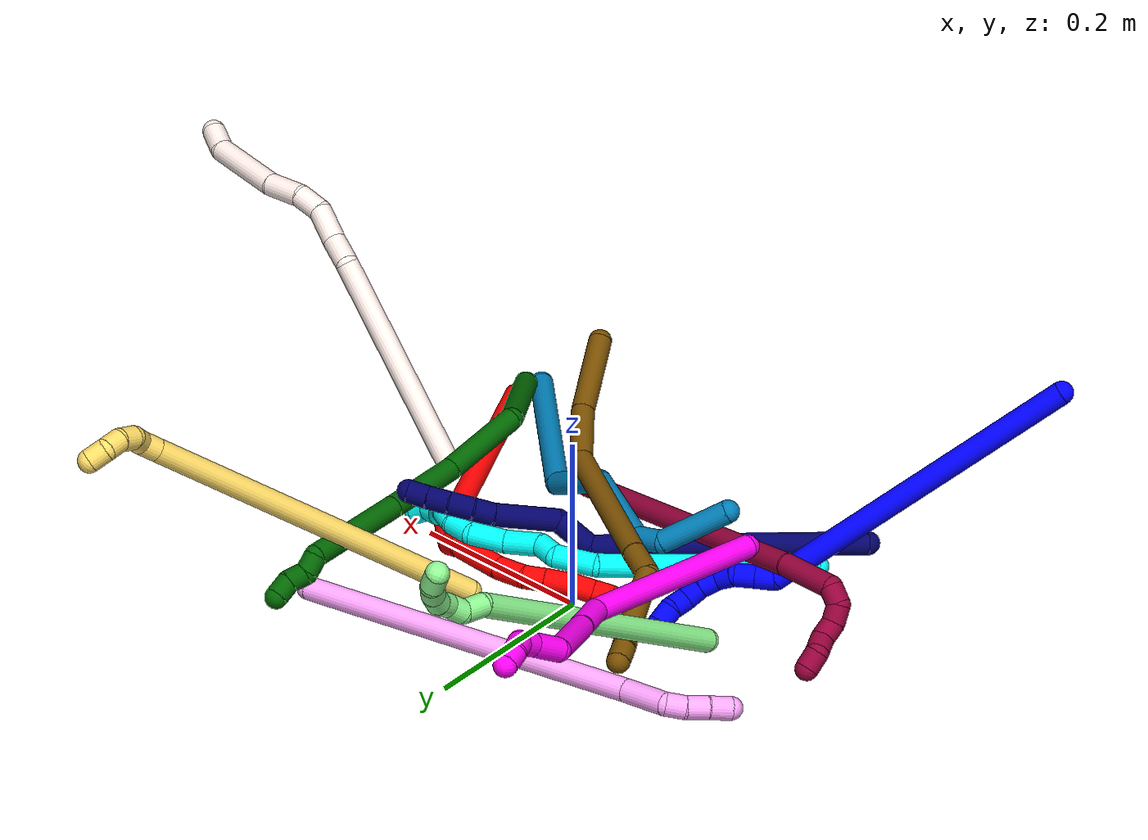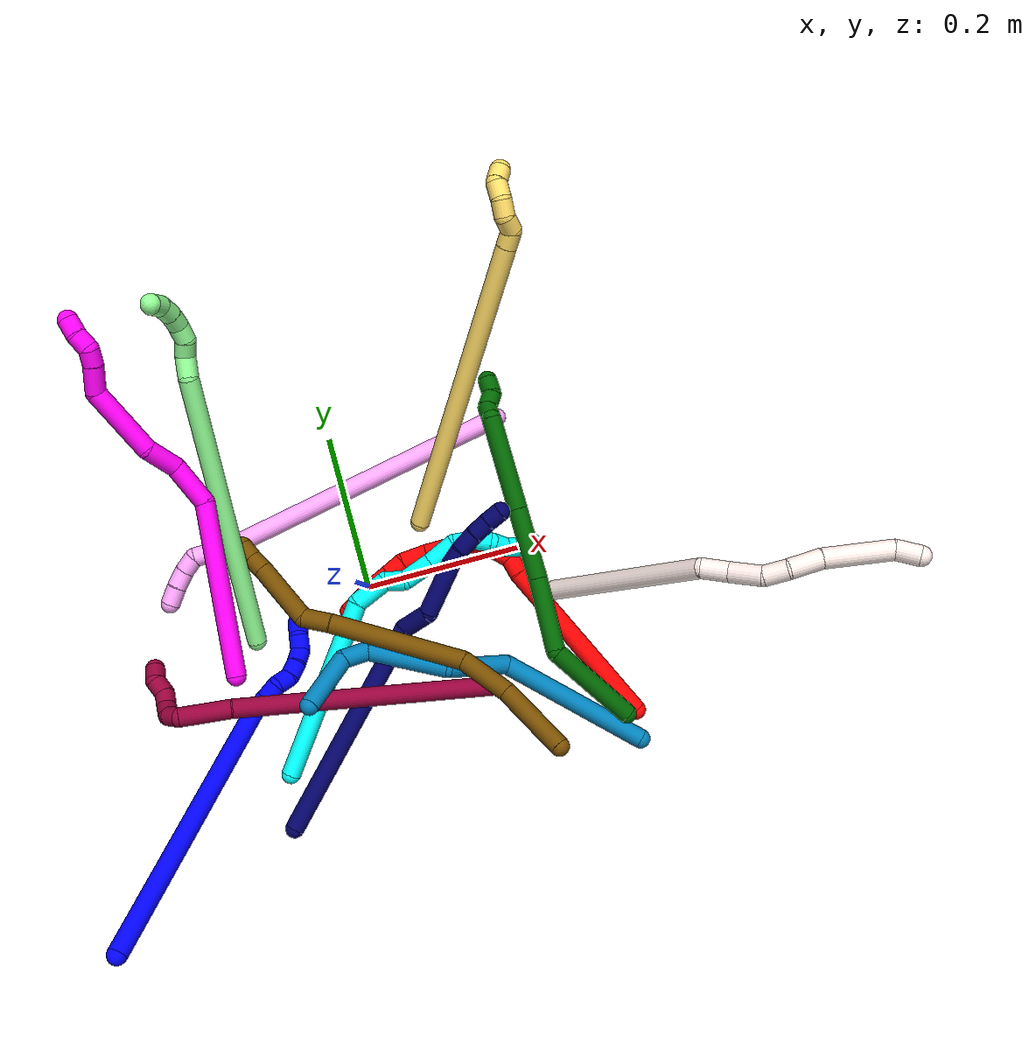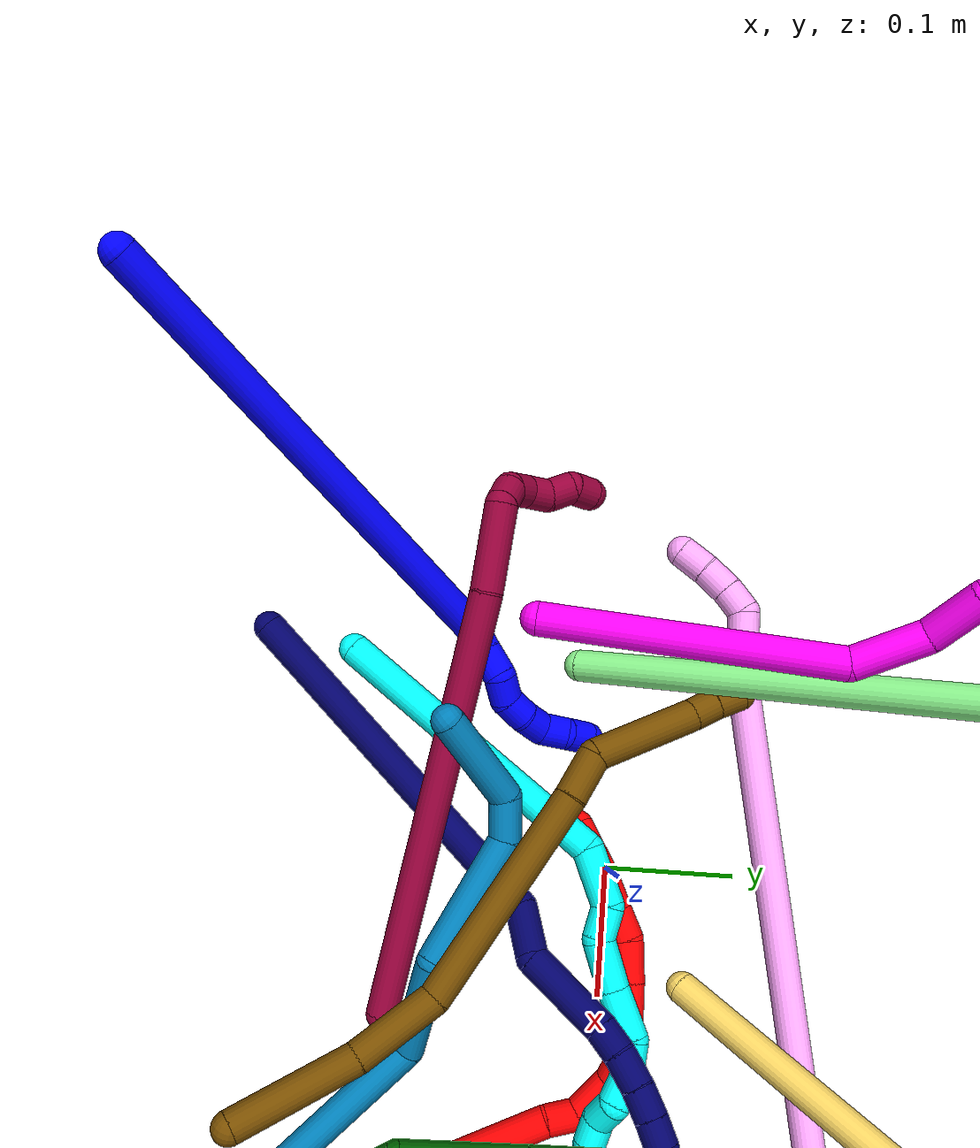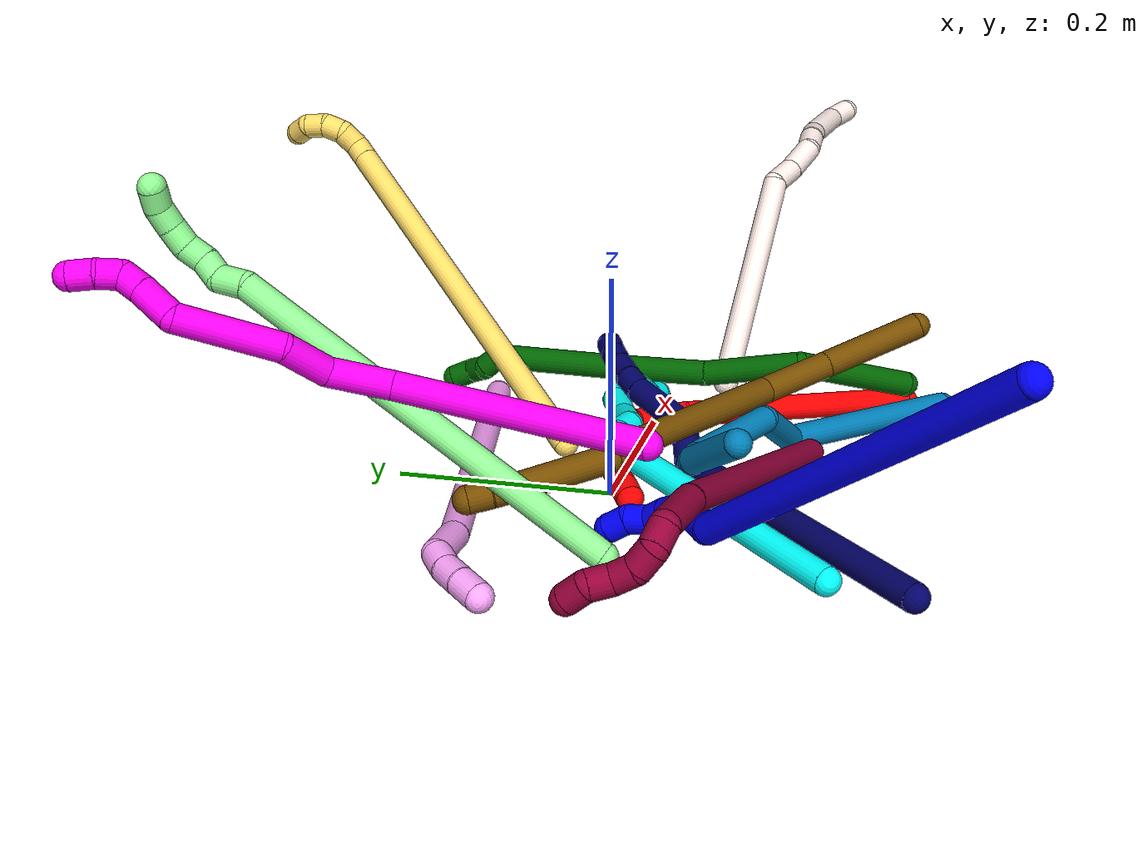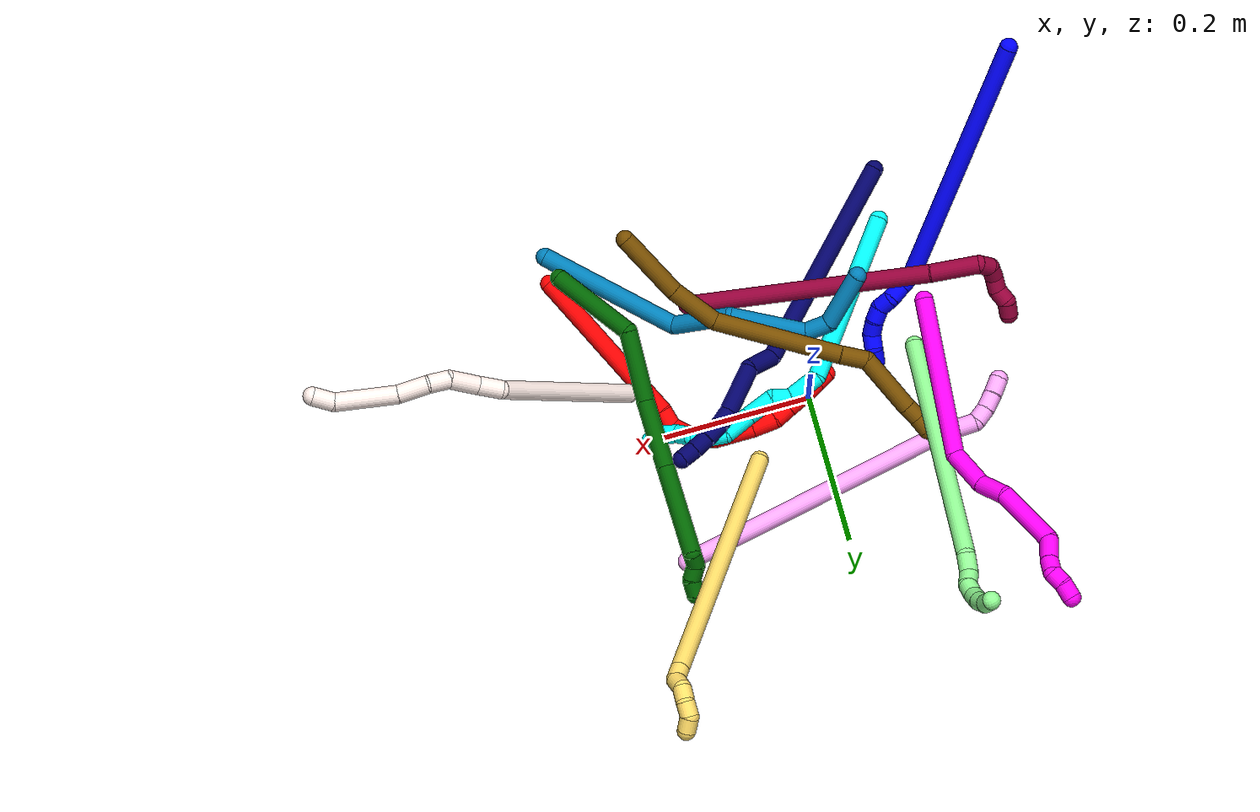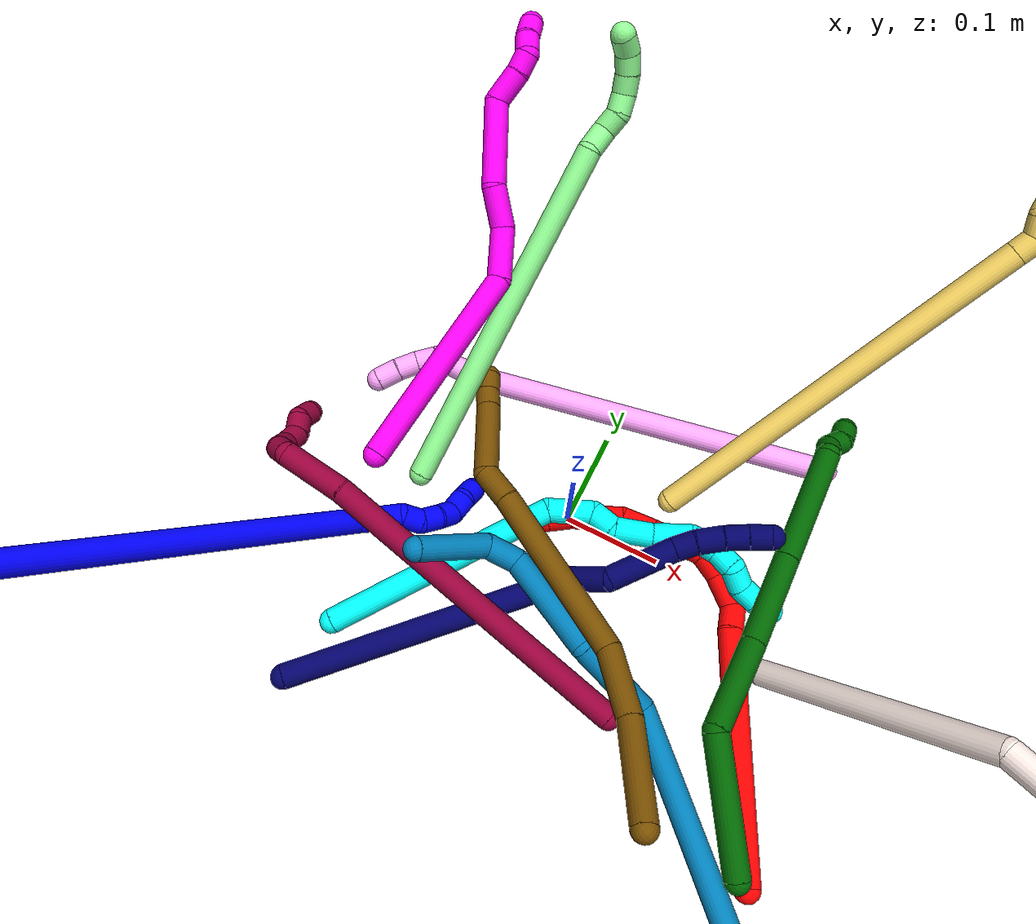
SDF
<sdf version="1.7">
 <world name="default">
  <plugin name="TubeGeneratorPlugin" filename="libtube_generator_plugin.so"/>
  <model name="photoneo_s_sensor">
   <static>1</static>
   <pose>0 0 2 1.57079 1.57079 3.14159</pose>
   <link name="link">
    <inertial><mass>0.1</mass></inertial>
    <sensor name="sensor" type="depth">
     <update_rate>30</update_rate>
     <camera>
      <horizontal_fov>1.22</horizontal_fov>
      <image><width>1920</width><height>1200</height><format>B8G8R8</format></image>
      <clip><near>0.1</near><far>4</far></clip>
      <depth_camera><output>points</output></depth_camera>
     </camera>
     <plugin name="camera_plugin" filename="libgazebo_ros_depth_camera.so">
      <baseline>0.2</baseline>
      <alwaysOn>1</alwaysOn>
      <updateRate>0.0</updateRate>
      <cameraName>camera_ir</cameraName>
      <imageTopicName>/camera/color/image_raw</imageTopicName>
      <cameraInfoTopicName>/camera/color/camera_info</cameraInfoTopicName>
      <depthImageTopicName>/camera/depth/image_raw</depthImageTopicName>
      <depthImageCameraInfoTopicName>/camera/depth/camera_info</depthImageCameraInfoTopicName>
      <pointCloudTopicName>/camera/depth/points</pointCloudTopicName>
      <frameName>fr_optical</frameName>
      <pointCloudCutoff>0.1</pointCloudCutoff>
      <pointCloudCutoffMax>2.0</pointCloudCutoffMax>
      <distortionK1>0</distortionK1>
      <distortionK2>0</distortionK2>
      <distortionK3>0</distortionK3>
      <distortionT1>0</distortionT1>
      <distortionT2>0</distortionT2>
      <CxPrime>0</CxPrime>
      <Cx>0</Cx>
      <Cy>0</Cy>
      <focalLength>0</focalLength>
      <hackBaseline>0</hackBaseline>
     </plugin>
    </sensor>
   </link>
  </model>
  <gravity>0 0 -9.8</gravity>
  <magnetic_field>6e-06 2.3e-05 -4.2e-05</magnetic_field>
  <atmosphere type="adiabatic"/>
  <physics name="default_physics" default="0" type="ode">
   <max_step_size>0.003</max_step_size>
   <real_time_factor>1</real_time_factor>
   <real_time_update_rate>1000</real_time_update_rate>
   <max_contacts>10000</max_contacts>
   <ode>
    <solver>
     <type>quick</type>
     <iters>100</iters>
     <sor>1.3</sor>
     <use_dynamic_moi_rescaling>0</use_dynamic_moi_rescaling>
    </solver>
    <constraints>
     <contact_max_correcting_vel>0</contact_max_correcting_vel>
     <contact_surface_layer>0.001</contact_surface_layer>
     <cfm>0</cfm>
     <erp>0.2</erp>
    </constraints>
   </ode>
  </physics>
  <scene><ambient>0.4 0.4 0.4 1</ambient><background>0.7 0.7 0.7 1</background><shadows>0</shadows></scene>
  <audio><device>default</device></audio>
  <spherical_coordinates>
   <surface_model>EARTH_WGS84</surface_model>
   <latitude_deg>0</latitude_deg>
   <longitude_deg>0</longitude_deg>
   <elevation>0</elevation>
   <heading_deg>0</heading_deg>
  </spherical_coordinates>
  <model name="bin">
   <static>1</static>
   <link name="bottom">
    <collision name="collision-bottom">
     <pose>0 0 -0.01 0 -0 0</pose>
     <geometry><box><size>0.8 0.6 0.02</size></box></geometry>
     <surface>
      <friction><ode><mu>100</mu><mu2>100</mu2></ode></friction>
      <contact><collide_bitmask>65535</collide_bitmask></contact>
     </surface>
    </collision>
   </link>
   <link name="west_wall">
    <collision name="collision-west_wall">
     <pose>-0.41 0 0.1 0 -0 0</pose>
     <geometry><box><size>0.02 0.6 0.2</size></box></geometry>
     <surface>
      <friction><ode><mu>100</mu><mu2>100</mu2></ode></friction>
      <contact><collide_bitmask>65535</collide_bitmask></contact>
     </surface>
    </collision>
   </link>
   <link name="east_wall">
    <collision name="collision-east_wall">
     <pose>0.41 0 0.1 0 -0 0</pose>
     <geometry><box><size>0.02 0.6 0.2</size></box></geometry>
     <surface>
      <friction><ode><mu>100</mu><mu2>100</mu2></ode></friction>
      <contact><collide_bitmask>65535</collide_bitmask></contact>
     </surface>
    </collision>
   </link>
   <link name="south_wall">
    <collision name="collision-south_wall">
     <pose>0 -0.31 0.1 0 -0 0</pose>
     <geometry><box><size>0.8 0.02 0.2</size></box></geometry>
     <surface>
      <friction><ode><mu>100</mu><mu2>100</mu2></ode></friction>
      <contact><collide_bitmask>65535</collide_bitmask></contact>
     </surface>
    </collision>
   </link>
   <link name="north_wall">
    <collision name="collision-north_wall">
     <pose>0 0.31 0.1 0 -0 0</pose>
     <geometry><box><size>0.8 0.02 0.2</size></box></geometry>
     <surface>
      <friction><ode><mu>100</mu><mu2>100</mu2></ode></friction>
      <contact><collide_bitmask>65535</collide_bitmask></contact>
     </surface>
    </collision>
   </link>
  </model>
  <model name="1">
   <static>0</static>
   <link name="1">
    <collision name="collision-cylinder-e_1_1_4">
     <pose>-0.014514 0.014615 -0.177175 -3.05929 -0.081458 1.56045</pose>
     <geometry><cylinder><radius>0.0125</radius><length>0.356736</length></cylinder></geometry>
     <surface>
      <friction><ode><mu>1.16</mu><mu2>1.16</mu2><slip1>0</slip1><slip2>0</slip2></ode></friction>
      <contact><ode><kp>1e+06</kp><kd>1</kd><max_vel>0</max_vel><min_depth>0.001</min_depth></ode></contact>
     </surface>
    </collision>
    <visual name="visual-cylinder-e_1_1_4">
     <pose>-0.014514 0.014615 -0.177175 -3.05929 -0.081458 1.56045</pose>
     <geometry><cylinder><radius>0.0125</radius><length>0.356736</length></cylinder></geometry>
     <material><ambient>0 0 1 1</ambient></material>
    </visual>
    <collision name="collision-cylinder-e_2_4_5">
     <pose>-0.023512 0.027339 -0.3632 2.9311 0.547267 2.42164</pose>
     <geometry><cylinder><radius>0.0125</radius><length>0.021197</length></cylinder></geometry>
     <surface>
      <friction><ode><mu>1.16</mu><mu2>1.16</mu2><slip1>0</slip1><slip2>0</slip2></ode></friction>
      <contact><ode><kp>1e+06</kp><kd>1</kd><max_vel>0</max_vel><min_depth>0.001</min_depth></ode></contact>
     </surface>
    </collision>
    <visual name="visual-cylinder-e_2_4_5">
     <pose>-0.023512 0.027339 -0.3632 2.9311 0.547267 2.42164</pose>
     <geometry><cylinder><radius>0.0125</radius><length>0.021197</length></cylinder></geometry>
     <material><ambient>0 0 1 1</ambient></material>
    </visual>
    <collision name="collision-cylinder-e_3_5_6">
     <pose>-0.012297 0.023876 -0.381154 2.97053 0.552863 2.55458</pose>
     <geometry><cylinder><radius>0.0125</radius><length>0.021708</length></cylinder></geometry>
     <surface>
      <friction><ode><mu>1.16</mu><mu2>1.16</mu2><slip1>0</slip1><slip2>0</slip2></ode></friction>
      <contact><ode><kp>1e+06</kp><kd>1</kd><max_vel>0</max_vel><min_depth>0.001</min_depth></ode></contact>
     </surface>
    </collision>
    <visual name="visual-cylinder-e_3_5_6">
     <pose>-0.012297 0.023876 -0.381154 2.97053 0.552863 2.55458</pose>
     <geometry><cylinder><radius>0.0125</radius><length>0.021708</length></cylinder></geometry>
     <material><ambient>0 0 1 1</ambient></material>
    </visual>
    <collision name="collision-cylinder-e_4_6_7">
     <pose>-0.006338 0.018581 -0.399632 2.76368 0.025743 0.134416</pose>
     <geometry><cylinder><radius>0.0125</radius><length>0.020182</length></cylinder></geometry>
     <surface>
      <friction><ode><mu>1.16</mu><mu2>1.16</mu2><slip1>0</slip1><slip2>0</slip2></ode></friction>
      <contact><ode><kp>1e+06</kp><kd>1</kd><max_vel>0</max_vel><min_depth>0.001</min_depth></ode></contact>
     </surface>
    </collision>
    <visual name="visual-cylinder-e_4_6_7">
     <pose>-0.006338 0.018581 -0.399632 2.76368 0.025743 0.134416</pose>
     <geometry><cylinder><radius>0.0125</radius><length>0.020182</length></cylinder></geometry>
     <material><ambient>0 0 1 1</ambient></material>
    </visual>
    <collision name="collision-cylinder-e_5_7_8">
     <pose>-0.005213 0.01613 -0.418948 -3.01442 0.086072 -1.18927</pose>
     <geometry><cylinder><radius>0.0125</radius><length>0.020116</length></cylinder></geometry>
     <surface>
      <friction><ode><mu>1.16</mu><mu2>1.16</mu2><slip1>0</slip1><slip2>0</slip2></ode></friction>
      <contact><ode><kp>1e+06</kp><kd>1</kd><max_vel>0</max_vel><min_depth>0.001</min_depth></ode></contact>
     </surface>
    </collision>
    <visual name="visual-cylinder-e_5_7_8">
     <pose>-0.005213 0.01613 -0.418948 -3.01442 0.086072 -1.18927</pose>
     <geometry><cylinder><radius>0.0125</radius><length>0.020116</length></cylinder></geometry>
     <material><ambient>0 0 1 1</ambient></material>
    </visual>
    <collision name="collision-cylinder-e_6_8_9">
     <pose>-0.005509 0.01983 -0.438547 -2.8952 -0.116002 0.876996</pose>
     <geometry><cylinder><radius>0.0125</radius><length>0.020055</length></cylinder></geometry>
     <surface>
      <friction><ode><mu>1.16</mu><mu2>1.16</mu2><slip1>0</slip1><slip2>0</slip2></ode></friction>
      <contact><ode><kp>1e+06</kp><kd>1</kd><max_vel>0</max_vel><min_depth>0.001</min_depth></ode></contact>
     </surface>
    </collision>
    <visual name="visual-cylinder-e_6_8_9">
     <pose>-0.005509 0.01983 -0.438547 -2.8952 -0.116002 0.876996</pose>
     <geometry><cylinder><radius>0.0125</radius><length>0.020055</length></cylinder></geometry>
     <material><ambient>0 0 1 1</ambient></material>
    </visual>
    <collision name="collision-cylinder-e_7_9_10">
     <pose>-0.004209 0.02854 -0.455591 -2.43685 0.248535 -0.654921</pose>
     <geometry><cylinder><radius>0.0125</radius><length>0.020004</length></cylinder></geometry>
     <surface>
      <friction><ode><mu>1.16</mu><mu2>1.16</mu2><slip1>0</slip1><slip2>0</slip2></ode></friction>
      <contact><ode><kp>1e+06</kp><kd>1</kd><max_vel>0</max_vel><min_depth>0.001</min_depth></ode></contact>
     </surface>
    </collision>
    <visual name="visual-cylinder-e_7_9_10">
     <pose>-0.004209 0.02854 -0.455591 -2.43685 0.248535 -0.654921</pose>
     <geometry><cylinder><radius>0.0125</radius><length>0.020004</length></cylinder></geometry>
     <material><ambient>0 0 1 1</ambient></material>
    </visual>
    <collision name="collision-cylinder-e_8_10_2">
     <pose>-0.003389 0.04017 -0.471266 -2.56852 -0.164677 0.54617</pose>
     <geometry><cylinder><radius>0.0125</radius><length>0.020001</length></cylinder></geometry>
     <surface>
      <friction><ode><mu>1.16</mu><mu2>1.16</mu2><slip1>0</slip1><slip2>0</slip2></ode></friction>
      <contact><ode><kp>1e+06</kp><kd>1</kd><max_vel>0</max_vel><min_depth>0.001</min_depth></ode></contact>
     </surface>
    </collision>
    <visual name="visual-cylinder-e_8_10_2">
     <pose>-0.003389 0.04017 -0.471266 -2.56852 -0.164677 0.54617</pose>
     <geometry><cylinder><radius>0.0125</radius><length>0.020001</length></cylinder></geometry>
     <material><ambient>0 0 1 1</ambient></material>
    </visual>
    <collision name="collision-sphere-2">
     <pose>-0.005028 0.045519 -0.479555 0 -0 0</pose>
     <geometry><sphere><radius>0.0125</radius></sphere></geometry>
     <surface>
      <friction><ode><mu>1.16</mu><mu2>1.16</mu2><slip1>0</slip1><slip2>0</slip2></ode></friction>
      <contact><ode><kp>1e+06</kp><kd>1</kd><max_vel>0</max_vel><min_depth>0.001</min_depth></ode></contact>
     </surface>
    </collision>
    <visual name="visual-sphere-2">
     <pose>-0.005028 0.045519 -0.479555 0 -0 0</pose>
     <geometry><sphere><radius>0.0125</radius></sphere></geometry>
     <material><ambient>0 0 1 1</ambient></material>
    </visual>
    <collision name="collision-sphere-10">
     <pose>-0.001749 0.034821 -0.462976 0 -0 0</pose>
     <geometry><sphere><radius>0.0125</radius></sphere></geometry>
     <surface>
      <friction><ode><mu>1.16</mu><mu2>1.16</mu2><slip1>0</slip1><slip2>0</slip2></ode></friction>
      <contact><ode><kp>1e+06</kp><kd>1</kd><max_vel>0</max_vel><min_depth>0.001</min_depth></ode></contact>
     </surface>
    </collision>
    <visual name="visual-sphere-10">
     <pose>-0.001749 0.034821 -0.462976 0 -0 0</pose>
     <geometry><sphere><radius>0.0125</radius></sphere></geometry>
     <material><ambient>0 0 1 1</ambient></material>
    </visual>
    <collision name="collision-sphere-9">
     <pose>-0.00667 0.02226 -0.448206 0 -0 0</pose>
     <geometry><sphere><radius>0.0125</radius></sphere></geometry>
     <surface>
      <friction><ode><mu>1.16</mu><mu2>1.16</mu2><slip1>0</slip1><slip2>0</slip2></ode></friction>
      <contact><ode><kp>1e+06</kp><kd>1</kd><max_vel>0</max_vel><min_depth>0.001</min_depth></ode></contact>
     </surface>
    </collision>
    <visual name="visual-sphere-9">
     <pose>-0.00667 0.02226 -0.448206 0 -0 0</pose>
     <geometry><sphere><radius>0.0125</radius></sphere></geometry>
     <material><ambient>0 0 1 1</ambient></material>
    </visual>
    <collision name="collision-sphere-4">
     <pose>-0.029027 0.02923 -0.354349 0 -0 0</pose>
     <geometry><sphere><radius>0.0125</radius></sphere></geometry>
     <surface>
      <friction><ode><mu>1.16</mu><mu2>1.16</mu2><slip1>0</slip1><slip2>0</slip2></ode></friction>
      <contact><ode><kp>1e+06</kp><kd>1</kd><max_vel>0</max_vel><min_depth>0.001</min_depth></ode></contact>
     </surface>
    </collision>
    <visual name="visual-sphere-4">
     <pose>-0.029027 0.02923 -0.354349 0 -0 0</pose>
     <geometry><sphere><radius>0.0125</radius></sphere></geometry>
     <material><ambient>0 0 1 1</ambient></material>
    </visual>
    <collision name="collision-sphere-1">
     <geometry><sphere><radius>0.0125</radius></sphere></geometry>
     <surface>
      <friction><ode><mu>1.16</mu><mu2>1.16</mu2><slip1>0</slip1><slip2>0</slip2></ode></friction>
      <contact><ode><kp>1e+06</kp><kd>1</kd><max_vel>0</max_vel><min_depth>0.001</min_depth></ode></contact>
     </surface>
    </collision>
    <visual name="visual-sphere-1">
     <geometry><sphere><radius>0.0125</radius></sphere></geometry>
     <material><ambient>0 0 1 1</ambient></material>
    </visual>
    <collision name="collision-sphere-8">
     <pose>-0.004348 0.017401 -0.428888 0 -0 0</pose>
     <geometry><sphere><radius>0.0125</radius></sphere></geometry>
     <surface>
      <friction><ode><mu>1.16</mu><mu2>1.16</mu2><slip1>0</slip1><slip2>0</slip2></ode></friction>
      <contact><ode><kp>1e+06</kp><kd>1</kd><max_vel>0</max_vel><min_depth>0.001</min_depth></ode></contact>
     </surface>
    </collision>
    <visual name="visual-sphere-8">
     <pose>-0.004348 0.017401 -0.428888 0 -0 0</pose>
     <geometry><sphere><radius>0.0125</radius></sphere></geometry>
     <material><ambient>0 0 1 1</ambient></material>
    </visual>
    <collision name="collision-sphere-5">
     <pose>-0.017997 0.025448 -0.372051 0 -0 0</pose>
     <geometry><sphere><radius>0.0125</radius></sphere></geometry>
     <surface>
      <friction><ode><mu>1.16</mu><mu2>1.16</mu2><slip1>0</slip1><slip2>0</slip2></ode></friction>
      <contact><ode><kp>1e+06</kp><kd>1</kd><max_vel>0</max_vel><min_depth>0.001</min_depth></ode></contact>
     </surface>
    </collision>
    <visual name="visual-sphere-5">
     <pose>-0.017997 0.025448 -0.372051 0 -0 0</pose>
     <geometry><sphere><radius>0.0125</radius></sphere></geometry>
     <material><ambient>0 0 1 1</ambient></material>
    </visual>
    <collision name="collision-sphere-6">
     <pose>-0.006597 0.022303 -0.390256 0 -0 0</pose>
     <geometry><sphere><radius>0.0125</radius></sphere></geometry>
     <surface>
      <friction><ode><mu>1.16</mu><mu2>1.16</mu2><slip1>0</slip1><slip2>0</slip2></ode></friction>
      <contact><ode><kp>1e+06</kp><kd>1</kd><max_vel>0</max_vel><min_depth>0.001</min_depth></ode></contact>
     </surface>
    </collision>
    <visual name="visual-sphere-6">
     <pose>-0.006597 0.022303 -0.390256 0 -0 0</pose>
     <geometry><sphere><radius>0.0125</radius></sphere></geometry>
     <material><ambient>0 0 1 1</ambient></material>
    </visual>
    <collision name="collision-sphere-7">
     <pose>-0.006078 0.014859 -0.409008 0 -0 0</pose>
     <geometry><sphere><radius>0.0125</radius></sphere></geometry>
     <surface>
      <friction><ode><mu>1.16</mu><mu2>1.16</mu2><slip1>0</slip1><slip2>0</slip2></ode></friction>
      <contact><ode><kp>1e+06</kp><kd>1</kd><max_vel>0</max_vel><min_depth>0.001</min_depth></ode></contact>
     </surface>
    </collision>
    <visual name="visual-sphere-7">
     <pose>-0.006078 0.014859 -0.409008 0 -0 0</pose>
     <geometry><sphere><radius>0.0125</radius></sphere></geometry>
     <material><ambient>0 0 1 1</ambient></material>
    </visual>
    <inertial>
     <pose>-0.012876 0.017566 -0.246011 0 -0 0</pose>
     <mass>0.5</mass>
     <inertia>
      <ixx>0.003828</ixx>
      <ixy>0</ixy>
      <ixz>0</ixz>
      <iyy>0.003774</iyy>
      <iyz>0</iyz>
      <izz>-4.3e-05</izz>
     </inertia>
    </inertial>
   </link>
   <pose>-0.366342 -0.342227 0.252897 0.05197 -1.05018 0.708383</pose>
  </model>
  <model name="2">
   <static>0</static>
   <link name="2">
    <collision name="collision-cylinder-e_1_1_4">
     <pose>0.017732 0.05914 -0.097939 -2.59835 0.153761 -0.539691</pose>
     <geometry><cylinder><radius>0.0125</radius><length>0.231552</length></cylinder></geometry>
     <surface>
      <friction><ode><mu>1.16</mu><mu2>1.16</mu2><slip1>0</slip1><slip2>0</slip2></ode></friction>
      <contact><ode><kp>1e+06</kp><kd>1</kd><max_vel>0</max_vel><min_depth>0.001</min_depth></ode></contact>
     </surface>
    </collision>
    <visual name="visual-cylinder-e_1_1_4">
     <pose>0.017732 0.05914 -0.097939 -2.59835 0.153761 -0.539691</pose>
     <geometry><cylinder><radius>0.0125</radius><length>0.231552</length></cylinder></geometry>
     <material><ambient>1 0 0 1</ambient></material>
    </visual>
    <collision name="collision-cylinder-e_2_4_5">
     <pose>0.039132 0.12261 -0.206584 -2.7573 0.307576 -1.34555</pose>
     <geometry><cylinder><radius>0.0125</radius><length>0.024233</length></cylinder></geometry>
     <surface>
      <friction><ode><mu>1.16</mu><mu2>1.16</mu2><slip1>0</slip1><slip2>0</slip2></ode></friction>
      <contact><ode><kp>1e+06</kp><kd>1</kd><max_vel>0</max_vel><min_depth>0.001</min_depth></ode></contact>
     </surface>
    </collision>
    <visual name="visual-cylinder-e_2_4_5">
     <pose>0.039132 0.12261 -0.206584 -2.7573 0.307576 -1.34555</pose>
     <geometry><cylinder><radius>0.0125</radius><length>0.024233</length></cylinder></geometry>
     <material><ambient>1 0 0 1</ambient></material>
    </visual>
    <collision name="collision-cylinder-e_3_5_6">
     <pose>0.038891 0.137725 -0.231166 -2.48084 -0.218848 0.620039</pose>
     <geometry><cylinder><radius>0.0125</radius><length>0.036008</length></cylinder></geometry>
     <surface>
      <friction><ode><mu>1.16</mu><mu2>1.16</mu2><slip1>0</slip1><slip2>0</slip2></ode></friction>
      <contact><ode><kp>1e+06</kp><kd>1</kd><max_vel>0</max_vel><min_depth>0.001</min_depth></ode></contact>
     </surface>
    </collision>
    <visual name="visual-cylinder-e_3_5_6">
     <pose>0.038891 0.137725 -0.231166 -2.48084 -0.218848 0.620039</pose>
     <geometry><cylinder><radius>0.0125</radius><length>0.036008</length></cylinder></geometry>
     <material><ambient>1 0 0 1</ambient></material>
    </visual>
    <collision name="collision-cylinder-e_4_6_7">
     <pose>0.029958 0.160301 -0.249522 -1.93399 -0.379085 0.542576</pose>
     <geometry><cylinder><radius>0.0125</radius><length>0.027153</length></cylinder></geometry>
     <surface>
      <friction><ode><mu>1.16</mu><mu2>1.16</mu2><slip1>0</slip1><slip2>0</slip2></ode></friction>
      <contact><ode><kp>1e+06</kp><kd>1</kd><max_vel>0</max_vel><min_depth>0.001</min_depth></ode></contact>
     </surface>
    </collision>
    <visual name="visual-cylinder-e_4_6_7">
     <pose>0.029958 0.160301 -0.249522 -1.93399 -0.379085 0.542576</pose>
     <geometry><cylinder><radius>0.0125</radius><length>0.027153</length></cylinder></geometry>
     <material><ambient>1 0 0 1</ambient></material>
    </visual>
    <collision name="collision-cylinder-e_5_7_8">
     <pose>0.003154 0.183658 -0.264296 -2.29796 -0.952763 1.71002</pose>
     <geometry><cylinder><radius>0.0125</radius><length>0.053446</length></cylinder></geometry>
     <surface>
      <friction><ode><mu>1.16</mu><mu2>1.16</mu2><slip1>0</slip1><slip2>0</slip2></ode></friction>
      <contact><ode><kp>1e+06</kp><kd>1</kd><max_vel>0</max_vel><min_depth>0.001</min_depth></ode></contact>
     </surface>
    </collision>
    <visual name="visual-cylinder-e_5_7_8">
     <pose>0.003154 0.183658 -0.264296 -2.29796 -0.952763 1.71002</pose>
     <geometry><cylinder><radius>0.0125</radius><length>0.053446</length></cylinder></geometry>
     <material><ambient>1 0 0 1</ambient></material>
    </visual>
    <collision name="collision-cylinder-e_6_8_9">
     <pose>-0.032232 0.203644 -0.278775 -2.03222 -0.966158 1.40503</pose>
     <geometry><cylinder><radius>0.0125</radius><length>0.033077</length></cylinder></geometry>
     <surface>
      <friction><ode><mu>1.16</mu><mu2>1.16</mu2><slip1>0</slip1><slip2>0</slip2></ode></friction>
      <contact><ode><kp>1e+06</kp><kd>1</kd><max_vel>0</max_vel><min_depth>0.001</min_depth></ode></contact>
     </surface>
    </collision>
    <visual name="visual-cylinder-e_6_8_9">
     <pose>-0.032232 0.203644 -0.278775 -2.03222 -0.966158 1.40503</pose>
     <geometry><cylinder><radius>0.0125</radius><length>0.033077</length></cylinder></geometry>
     <material><ambient>1 0 0 1</ambient></material>
    </visual>
    <collision name="collision-cylinder-e_7_9_10">
     <pose>-0.056974 0.21577 -0.282727 -1.50793 -1.24877 1.18972</pose>
     <geometry><cylinder><radius>0.0125</radius><length>0.023478</length></cylinder></geometry>
     <surface>
      <friction><ode><mu>1.16</mu><mu2>1.16</mu2><slip1>0</slip1><slip2>0</slip2></ode></friction>
      <contact><ode><kp>1e+06</kp><kd>1</kd><max_vel>0</max_vel><min_depth>0.001</min_depth></ode></contact>
     </surface>
    </collision>
    <visual name="visual-cylinder-e_7_9_10">
     <pose>-0.056974 0.21577 -0.282727 -1.50793 -1.24877 1.18972</pose>
     <geometry><cylinder><radius>0.0125</radius><length>0.023478</length></cylinder></geometry>
     <material><ambient>1 0 0 1</ambient></material>
    </visual>
    <collision name="collision-cylinder-e_8_10_11">
     <pose>-0.081487 0.223707 -0.282733 -1.62737 -1.26417 1.31857</pose>
     <geometry><cylinder><radius>0.0125</radius><length>0.028064</length></cylinder></geometry>
     <surface>
      <friction><ode><mu>1.16</mu><mu2>1.16</mu2><slip1>0</slip1><slip2>0</slip2></ode></friction>
      <contact><ode><kp>1e+06</kp><kd>1</kd><max_vel>0</max_vel><min_depth>0.001</min_depth></ode></contact>
     </surface>
    </collision>
    <visual name="visual-cylinder-e_8_10_11">
     <pose>-0.081487 0.223707 -0.282733 -1.62737 -1.26417 1.31857</pose>
     <geometry><cylinder><radius>0.0125</radius><length>0.028064</length></cylinder></geometry>
     <material><ambient>1 0 0 1</ambient></material>
    </visual>
    <collision name="collision-cylinder-e_9_11_12">
     <pose>-0.106236 0.22877 -0.28347 -2.10788 -1.48562 2.03306</pose>
     <geometry><cylinder><radius>0.0125</radius><length>0.022827</length></cylinder></geometry>
     <surface>
      <friction><ode><mu>1.16</mu><mu2>1.16</mu2><slip1>0</slip1><slip2>0</slip2></ode></friction>
      <contact><ode><kp>1e+06</kp><kd>1</kd><max_vel>0</max_vel><min_depth>0.001</min_depth></ode></contact>
     </surface>
    </collision>
    <visual name="visual-cylinder-e_9_11_12">
     <pose>-0.106236 0.22877 -0.28347 -2.10788 -1.48562 2.03306</pose>
     <geometry><cylinder><radius>0.0125</radius><length>0.022827</length></cylinder></geometry>
     <material><ambient>1 0 0 1</ambient></material>
    </visual>
    <collision name="collision-cylinder-e_10_12_2">
     <pose>-0.127649 0.230403 -0.284392 -2.0608 -1.48091 1.97977</pose>
     <geometry><cylinder><radius>0.0125</radius><length>0.020162</length></cylinder></geometry>
     <surface>
      <friction><ode><mu>1.16</mu><mu2>1.16</mu2><slip1>0</slip1><slip2>0</slip2></ode></friction>
      <contact><ode><kp>1e+06</kp><kd>1</kd><max_vel>0</max_vel><min_depth>0.001</min_depth></ode></contact>
     </surface>
    </collision>
    <visual name="visual-cylinder-e_10_12_2">
     <pose>-0.127649 0.230403 -0.284392 -2.0608 -1.48091 1.97977</pose>
     <geometry><cylinder><radius>0.0125</radius><length>0.020162</length></cylinder></geometry>
     <material><ambient>1 0 0 1</ambient></material>
    </visual>
    <collision name="collision-sphere-2">
     <pose>-0.137689 0.231201 -0.284818 0 -0 0</pose>
     <geometry><sphere><radius>0.0125</radius></sphere></geometry>
     <surface>
      <friction><ode><mu>1.16</mu><mu2>1.16</mu2><slip1>0</slip1><slip2>0</slip2></ode></friction>
      <contact><ode><kp>1e+06</kp><kd>1</kd><max_vel>0</max_vel><min_depth>0.001</min_depth></ode></contact>
     </surface>
    </collision>
    <visual name="visual-sphere-2">
     <pose>-0.137689 0.231201 -0.284818 0 -0 0</pose>
     <geometry><sphere><radius>0.0125</radius></sphere></geometry>
     <material><ambient>1 0 0 1</ambient></material>
    </visual>
    <collision name="collision-sphere-12">
     <pose>-0.117608 0.229604 -0.283966 0 -0 0</pose>
     <geometry><sphere><radius>0.0125</radius></sphere></geometry>
     <surface>
      <friction><ode><mu>1.16</mu><mu2>1.16</mu2><slip1>0</slip1><slip2>0</slip2></ode></friction>
      <contact><ode><kp>1e+06</kp><kd>1</kd><max_vel>0</max_vel><min_depth>0.001</min_depth></ode></contact>
     </surface>
    </collision>
    <visual name="visual-sphere-12">
     <pose>-0.117608 0.229604 -0.283966 0 -0 0</pose>
     <geometry><sphere><radius>0.0125</radius></sphere></geometry>
     <material><ambient>1 0 0 1</ambient></material>
    </visual>
    <collision name="collision-sphere-11">
     <pose>-0.094864 0.227936 -0.282973 0 -0 0</pose>
     <geometry><sphere><radius>0.0125</radius></sphere></geometry>
     <surface>
      <friction><ode><mu>1.16</mu><mu2>1.16</mu2><slip1>0</slip1><slip2>0</slip2></ode></friction>
      <contact><ode><kp>1e+06</kp><kd>1</kd><max_vel>0</max_vel><min_depth>0.001</min_depth></ode></contact>
     </surface>
    </collision>
    <visual name="visual-sphere-11">
     <pose>-0.094864 0.227936 -0.282973 0 -0 0</pose>
     <geometry><sphere><radius>0.0125</radius></sphere></geometry>
     <material><ambient>1 0 0 1</ambient></material>
    </visual>
    <collision name="collision-sphere-10">
     <pose>-0.068109 0.219478 -0.282494 0 -0 0</pose>
     <geometry><sphere><radius>0.0125</radius></sphere></geometry>
     <surface>
      <friction><ode><mu>1.16</mu><mu2>1.16</mu2><slip1>0</slip1><slip2>0</slip2></ode></friction>
      <contact><ode><kp>1e+06</kp><kd>1</kd><max_vel>0</max_vel><min_depth>0.001</min_depth></ode></contact>
     </surface>
    </collision>
    <visual name="visual-sphere-10">
     <pose>-0.068109 0.219478 -0.282494 0 -0 0</pose>
     <geometry><sphere><radius>0.0125</radius></sphere></geometry>
     <material><ambient>1 0 0 1</ambient></material>
    </visual>
    <collision name="collision-sphere-9">
     <pose>-0.045838 0.212062 -0.282961 0 -0 0</pose>
     <geometry><sphere><radius>0.0125</radius></sphere></geometry>
     <surface>
      <friction><ode><mu>1.16</mu><mu2>1.16</mu2><slip1>0</slip1><slip2>0</slip2></ode></friction>
      <contact><ode><kp>1e+06</kp><kd>1</kd><max_vel>0</max_vel><min_depth>0.001</min_depth></ode></contact>
     </surface>
    </collision>
    <visual name="visual-sphere-9">
     <pose>-0.045838 0.212062 -0.282961 0 -0 0</pose>
     <geometry><sphere><radius>0.0125</radius></sphere></geometry>
     <material><ambient>1 0 0 1</ambient></material>
    </visual>
    <collision name="collision-sphere-4">
     <pose>0.035463 0.11828 -0.195878 0 -0 0</pose>
     <geometry><sphere><radius>0.0125</radius></sphere></geometry>
     <surface>
      <friction><ode><mu>1.16</mu><mu2>1.16</mu2><slip1>0</slip1><slip2>0</slip2></ode></friction>
      <contact><ode><kp>1e+06</kp><kd>1</kd><max_vel>0</max_vel><min_depth>0.001</min_depth></ode></contact>
     </surface>
    </collision>
    <visual name="visual-sphere-4">
     <pose>0.035463 0.11828 -0.195878 0 -0 0</pose>
     <geometry><sphere><radius>0.0125</radius></sphere></geometry>
     <material><ambient>1 0 0 1</ambient></material>
    </visual>
    <collision name="collision-sphere-1">
     <geometry><sphere><radius>0.0125</radius></sphere></geometry>
     <surface>
      <friction><ode><mu>1.16</mu><mu2>1.16</mu2><slip1>0</slip1><slip2>0</slip2></ode></friction>
      <contact><ode><kp>1e+06</kp><kd>1</kd><max_vel>0</max_vel><min_depth>0.001</min_depth></ode></contact>
     </surface>
    </collision>
    <visual name="visual-sphere-1">
     <geometry><sphere><radius>0.0125</radius></sphere></geometry>
     <material><ambient>1 0 0 1</ambient></material>
    </visual>
    <collision name="collision-sphere-8">
     <pose>-0.018626 0.195226 -0.274589 0 -0 0</pose>
     <geometry><sphere><radius>0.0125</radius></sphere></geometry>
     <surface>
      <friction><ode><mu>1.16</mu><mu2>1.16</mu2><slip1>0</slip1><slip2>0</slip2></ode></friction>
      <contact><ode><kp>1e+06</kp><kd>1</kd><max_vel>0</max_vel><min_depth>0.001</min_depth></ode></contact>
     </surface>
    </collision>
    <visual name="visual-sphere-8">
     <pose>-0.018626 0.195226 -0.274589 0 -0 0</pose>
     <geometry><sphere><radius>0.0125</radius></sphere></geometry>
     <material><ambient>1 0 0 1</ambient></material>
    </visual>
    <collision name="collision-sphere-5">
     <pose>0.0428 0.126939 -0.21729 0 -0 0</pose>
     <geometry><sphere><radius>0.0125</radius></sphere></geometry>
     <surface>
      <friction><ode><mu>1.16</mu><mu2>1.16</mu2><slip1>0</slip1><slip2>0</slip2></ode></friction>
      <contact><ode><kp>1e+06</kp><kd>1</kd><max_vel>0</max_vel><min_depth>0.001</min_depth></ode></contact>
     </surface>
    </collision>
    <visual name="visual-sphere-5">
     <pose>0.0428 0.126939 -0.21729 0 -0 0</pose>
     <geometry><sphere><radius>0.0125</radius></sphere></geometry>
     <material><ambient>1 0 0 1</ambient></material>
    </visual>
    <collision name="collision-sphere-6">
     <pose>0.034982 0.148511 -0.245041 0 -0 0</pose>
     <geometry><sphere><radius>0.0125</radius></sphere></geometry>
     <surface>
      <friction><ode><mu>1.16</mu><mu2>1.16</mu2><slip1>0</slip1><slip2>0</slip2></ode></friction>
      <contact><ode><kp>1e+06</kp><kd>1</kd><max_vel>0</max_vel><min_depth>0.001</min_depth></ode></contact>
     </surface>
    </collision>
    <visual name="visual-sphere-6">
     <pose>0.034982 0.148511 -0.245041 0 -0 0</pose>
     <geometry><sphere><radius>0.0125</radius></sphere></geometry>
     <material><ambient>1 0 0 1</ambient></material>
    </visual>
    <collision name="collision-sphere-7">
     <pose>0.024934 0.172091 -0.254003 0 -0 0</pose>
     <geometry><sphere><radius>0.0125</radius></sphere></geometry>
     <surface>
      <friction><ode><mu>1.16</mu><mu2>1.16</mu2><slip1>0</slip1><slip2>0</slip2></ode></friction>
      <contact><ode><kp>1e+06</kp><kd>1</kd><max_vel>0</max_vel><min_depth>0.001</min_depth></ode></contact>
     </surface>
    </collision>
    <visual name="visual-sphere-7">
     <pose>0.024934 0.172091 -0.254003 0 -0 0</pose>
     <geometry><sphere><radius>0.0125</radius></sphere></geometry>
     <material><ambient>1 0 0 1</ambient></material>
    </visual>
    <inertial>
     <pose>-0.004506 0.127481 -0.185814 0 -0 0</pose>
     <mass>0.5</mass>
     <inertia>
      <ixx>0.000365</ixx>
      <ixy>0</ixy>
      <ixz>0</ixz>
      <iyy>-0.001204</iyy>
      <iyz>0</iyz>
      <izz>-0.000707</izz>
     </inertia>
    </inertial>
   </link>
   <pose>0.293817 -0.24317 0.013495 0.986913 -0.268938 0.607638</pose>
  </model>
  <model name="3">
   <static>0</static>
   <link name="3">
    <collision name="collision-cylinder-e_1_1_4">
     <pose>0.028494 0.08128 -0.083223 -2.36801 0.24021 -0.576117</pose>
     <geometry><cylinder><radius>0.0125</radius><length>0.239537</length></cylinder></geometry>
     <surface>
      <friction><ode><mu>1.16</mu><mu2>1.16</mu2><slip1>0</slip1><slip2>0</slip2></ode></friction>
      <contact><ode><kp>1e+06</kp><kd>1</kd><max_vel>0</max_vel><min_depth>0.001</min_depth></ode></contact>
     </surface>
    </collision>
    <visual name="visual-cylinder-e_1_1_4">
     <pose>0.028494 0.08128 -0.083223 -2.36801 0.24021 -0.576117</pose>
     <geometry><cylinder><radius>0.0125</radius><length>0.239537</length></cylinder></geometry>
     <material><ambient>0.003922 1 0.996078 1</ambient></material>
    </visual>
    <collision name="collision-cylinder-e_2_4_5">
     <pose>0.068311 0.167903 -0.185135 -2.86309 0.527493 -2.18409</pose>
     <geometry><cylinder><radius>0.0125</radius><length>0.04499</length></cylinder></geometry>
     <surface>
      <friction><ode><mu>1.16</mu><mu2>1.16</mu2><slip1>0</slip1><slip2>0</slip2></ode></friction>
      <contact><ode><kp>1e+06</kp><kd>1</kd><max_vel>0</max_vel><min_depth>0.001</min_depth></ode></contact>
     </surface>
    </collision>
    <visual name="visual-cylinder-e_2_4_5">
     <pose>0.068311 0.167903 -0.185135 -2.86309 0.527493 -2.18409</pose>
     <geometry><cylinder><radius>0.0125</radius><length>0.04499</length></cylinder></geometry>
     <material><ambient>0.003922 1 0.996078 1</ambient></material>
    </visual>
    <collision name="collision-cylinder-e_3_5_6">
     <pose>0.088443 0.169227 -0.211919 2.68067 0.772524 2.09504</pose>
     <geometry><cylinder><radius>0.0125</radius><length>0.025242</length></cylinder></geometry>
     <surface>
      <friction><ode><mu>1.16</mu><mu2>1.16</mu2><slip1>0</slip1><slip2>0</slip2></ode></friction>
      <contact><ode><kp>1e+06</kp><kd>1</kd><max_vel>0</max_vel><min_depth>0.001</min_depth></ode></contact>
     </surface>
    </collision>
    <visual name="visual-cylinder-e_3_5_6">
     <pose>0.088443 0.169227 -0.211919 2.68067 0.772524 2.09504</pose>
     <geometry><cylinder><radius>0.0125</radius><length>0.025242</length></cylinder></geometry>
     <material><ambient>0.003922 1 0.996078 1</ambient></material>
    </visual>
    <collision name="collision-cylinder-e_4_6_7">
     <pose>0.104923 0.167318 -0.237907 -3.02416 0.402522 -2.58054</pose>
     <geometry><cylinder><radius>0.0125</radius><length>0.039164</length></cylinder></geometry>
     <surface>
      <friction><ode><mu>1.16</mu><mu2>1.16</mu2><slip1>0</slip1><slip2>0</slip2></ode></friction>
      <contact><ode><kp>1e+06</kp><kd>1</kd><max_vel>0</max_vel><min_depth>0.001</min_depth></ode></contact>
     </surface>
    </collision>
    <visual name="visual-cylinder-e_4_6_7">
     <pose>0.104923 0.167318 -0.237907 -3.02416 0.402522 -2.58054</pose>
     <geometry><cylinder><radius>0.0125</radius><length>0.039164</length></cylinder></geometry>
     <material><ambient>0.003922 1 0.996078 1</ambient></material>
    </visual>
    <collision name="collision-cylinder-e_5_7_8">
     <pose>0.122689 0.174693 -0.271749 -2.82276 0.541214 -2.09106</pose>
     <geometry><cylinder><radius>0.0125</radius><length>0.039192</length></cylinder></geometry>
     <surface>
      <friction><ode><mu>1.16</mu><mu2>1.16</mu2><slip1>0</slip1><slip2>0</slip2></ode></friction>
      <contact><ode><kp>1e+06</kp><kd>1</kd><max_vel>0</max_vel><min_depth>0.001</min_depth></ode></contact>
     </surface>
    </collision>
    <visual name="visual-cylinder-e_5_7_8">
     <pose>0.122689 0.174693 -0.271749 -2.82276 0.541214 -2.09106</pose>
     <geometry><cylinder><radius>0.0125</radius><length>0.039192</length></cylinder></geometry>
     <material><ambient>0.003922 1 0.996078 1</ambient></material>
    </visual>
    <collision name="collision-cylinder-e_6_8_9">
     <pose>0.141771 0.176955 -0.297695 2.84973 0.710785 2.38749</pose>
     <geometry><cylinder><radius>0.0125</radius><length>0.027547</length></cylinder></geometry>
     <surface>
      <friction><ode><mu>1.16</mu><mu2>1.16</mu2><slip1>0</slip1><slip2>0</slip2></ode></friction>
      <contact><ode><kp>1e+06</kp><kd>1</kd><max_vel>0</max_vel><min_depth>0.001</min_depth></ode></contact>
     </surface>
    </collision>
    <visual name="visual-cylinder-e_6_8_9">
     <pose>0.141771 0.176955 -0.297695 2.84973 0.710785 2.38749</pose>
     <geometry><cylinder><radius>0.0125</radius><length>0.027547</length></cylinder></geometry>
     <material><ambient>0.003922 1 0.996078 1</ambient></material>
    </visual>
    <collision name="collision-cylinder-e_7_9_10">
     <pose>0.158719 0.169394 -0.313248 2.45469 0.836598 1.78663</pose>
     <geometry><cylinder><radius>0.0125</radius><length>0.021451</length></cylinder></geometry>
     <surface>
      <friction><ode><mu>1.16</mu><mu2>1.16</mu2><slip1>0</slip1><slip2>0</slip2></ode></friction>
      <contact><ode><kp>1e+06</kp><kd>1</kd><max_vel>0</max_vel><min_depth>0.001</min_depth></ode></contact>
     </surface>
    </collision>
    <visual name="visual-cylinder-e_7_9_10">
     <pose>0.158719 0.169394 -0.313248 2.45469 0.836598 1.78663</pose>
     <geometry><cylinder><radius>0.0125</radius><length>0.021451</length></cylinder></geometry>
     <material><ambient>0.003922 1 0.996078 1</ambient></material>
    </visual>
    <collision name="collision-cylinder-e_8_10_11">
     <pose>0.168128 0.156344 -0.32602 2.27501 0.129058 0.27757</pose>
     <geometry><cylinder><radius>0.0125</radius><length>0.022475</length></cylinder></geometry>
     <surface>
      <friction><ode><mu>1.16</mu><mu2>1.16</mu2><slip1>0</slip1><slip2>0</slip2></ode></friction>
      <contact><ode><kp>1e+06</kp><kd>1</kd><max_vel>0</max_vel><min_depth>0.001</min_depth></ode></contact>
     </surface>
    </collision>
    <visual name="visual-cylinder-e_8_10_11">
     <pose>0.168128 0.156344 -0.32602 2.27501 0.129058 0.27757</pose>
     <geometry><cylinder><radius>0.0125</radius><length>0.022475</length></cylinder></geometry>
     <material><ambient>0.003922 1 0.996078 1</ambient></material>
    </visual>
    <collision name="collision-cylinder-e_9_11_12">
     <pose>0.174857 0.143334 -0.340528 2.58707 0.551939 1.56588</pose>
     <geometry><cylinder><radius>0.0125</radius><length>0.020149</length></cylinder></geometry>
     <surface>
      <friction><ode><mu>1.16</mu><mu2>1.16</mu2><slip1>0</slip1><slip2>0</slip2></ode></friction>
      <contact><ode><kp>1e+06</kp><kd>1</kd><max_vel>0</max_vel><min_depth>0.001</min_depth></ode></contact>
     </surface>
    </collision>
    <visual name="visual-cylinder-e_9_11_12">
     <pose>0.174857 0.143334 -0.340528 2.58707 0.551939 1.56588</pose>
     <geometry><cylinder><radius>0.0125</radius><length>0.020149</length></cylinder></geometry>
     <material><ambient>0.003922 1 0.996078 1</ambient></material>
    </visual>
    <collision name="collision-cylinder-e_10_12_2">
     <pose>0.181446 0.135566 -0.357322 2.81188 0.129405 0.742771</pose>
     <geometry><cylinder><radius>0.0125</radius><length>0.020252</length></cylinder></geometry>
     <surface>
      <friction><ode><mu>1.16</mu><mu2>1.16</mu2><slip1>0</slip1><slip2>0</slip2></ode></friction>
      <contact><ode><kp>1e+06</kp><kd>1</kd><max_vel>0</max_vel><min_depth>0.001</min_depth></ode></contact>
     </surface>
    </collision>
    <visual name="visual-cylinder-e_10_12_2">
     <pose>0.181446 0.135566 -0.357322 2.81188 0.129405 0.742771</pose>
     <geometry><cylinder><radius>0.0125</radius><length>0.020252</length></cylinder></geometry>
     <material><ambient>0.003922 1 0.996078 1</ambient></material>
    </visual>
    <collision name="collision-sphere-2">
     <pose>0.182753 0.132314 -0.366822 0 -0 0</pose>
     <geometry><sphere><radius>0.0125</radius></sphere></geometry>
     <surface>
      <friction><ode><mu>1.16</mu><mu2>1.16</mu2><slip1>0</slip1><slip2>0</slip2></ode></friction>
      <contact><ode><kp>1e+06</kp><kd>1</kd><max_vel>0</max_vel><min_depth>0.001</min_depth></ode></contact>
     </surface>
    </collision>
    <visual name="visual-sphere-2">
     <pose>0.182753 0.132314 -0.366822 0 -0 0</pose>
     <geometry><sphere><radius>0.0125</radius></sphere></geometry>
     <material><ambient>0.003922 1 0.996078 1</ambient></material>
    </visual>
    <collision name="collision-sphere-12">
     <pose>0.180139 0.138817 -0.347821 0 -0 0</pose>
     <geometry><sphere><radius>0.0125</radius></sphere></geometry>
     <surface>
      <friction><ode><mu>1.16</mu><mu2>1.16</mu2><slip1>0</slip1><slip2>0</slip2></ode></friction>
      <contact><ode><kp>1e+06</kp><kd>1</kd><max_vel>0</max_vel><min_depth>0.001</min_depth></ode></contact>
     </surface>
    </collision>
    <visual name="visual-sphere-12">
     <pose>0.180139 0.138817 -0.347821 0 -0 0</pose>
     <geometry><sphere><radius>0.0125</radius></sphere></geometry>
     <material><ambient>0.003922 1 0.996078 1</ambient></material>
    </visual>
    <collision name="collision-sphere-11">
     <pose>0.169574 0.147851 -0.333235 0 -0 0</pose>
     <geometry><sphere><radius>0.0125</radius></sphere></geometry>
     <surface>
      <friction><ode><mu>1.16</mu><mu2>1.16</mu2><slip1>0</slip1><slip2>0</slip2></ode></friction>
      <contact><ode><kp>1e+06</kp><kd>1</kd><max_vel>0</max_vel><min_depth>0.001</min_depth></ode></contact>
     </surface>
    </collision>
    <visual name="visual-sphere-11">
     <pose>0.169574 0.147851 -0.333235 0 -0 0</pose>
     <geometry><sphere><radius>0.0125</radius></sphere></geometry>
     <material><ambient>0.003922 1 0.996078 1</ambient></material>
    </visual>
    <collision name="collision-sphere-10">
     <pose>0.166682 0.164837 -0.318804 0 -0 0</pose>
     <geometry><sphere><radius>0.0125</radius></sphere></geometry>
     <surface>
      <friction><ode><mu>1.16</mu><mu2>1.16</mu2><slip1>0</slip1><slip2>0</slip2></ode></friction>
      <contact><ode><kp>1e+06</kp><kd>1</kd><max_vel>0</max_vel><min_depth>0.001</min_depth></ode></contact>
     </surface>
    </collision>
    <visual name="visual-sphere-10">
     <pose>0.166682 0.164837 -0.318804 0 -0 0</pose>
     <geometry><sphere><radius>0.0125</radius></sphere></geometry>
     <material><ambient>0.003922 1 0.996078 1</ambient></material>
    </visual>
    <collision name="collision-sphere-9">
     <pose>0.150757 0.173951 -0.307692 0 -0 0</pose>
     <geometry><sphere><radius>0.0125</radius></sphere></geometry>
     <surface>
      <friction><ode><mu>1.16</mu><mu2>1.16</mu2><slip1>0</slip1><slip2>0</slip2></ode></friction>
      <contact><ode><kp>1e+06</kp><kd>1</kd><max_vel>0</max_vel><min_depth>0.001</min_depth></ode></contact>
     </surface>
    </collision>
    <visual name="visual-sphere-9">
     <pose>0.150757 0.173951 -0.307692 0 -0 0</pose>
     <geometry><sphere><radius>0.0125</radius></sphere></geometry>
     <material><ambient>0.003922 1 0.996078 1</ambient></material>
    </visual>
    <collision name="collision-sphere-4">
     <pose>0.056987 0.16256 -0.166447 0 -0 0</pose>
     <geometry><sphere><radius>0.0125</radius></sphere></geometry>
     <surface>
      <friction><ode><mu>1.16</mu><mu2>1.16</mu2><slip1>0</slip1><slip2>0</slip2></ode></friction>
      <contact><ode><kp>1e+06</kp><kd>1</kd><max_vel>0</max_vel><min_depth>0.001</min_depth></ode></contact>
     </surface>
    </collision>
    <visual name="visual-sphere-4">
     <pose>0.056987 0.16256 -0.166447 0 -0 0</pose>
     <geometry><sphere><radius>0.0125</radius></sphere></geometry>
     <material><ambient>0.003922 1 0.996078 1</ambient></material>
    </visual>
    <collision name="collision-sphere-1">
     <geometry><sphere><radius>0.0125</radius></sphere></geometry>
     <surface>
      <friction><ode><mu>1.16</mu><mu2>1.16</mu2><slip1>0</slip1><slip2>0</slip2></ode></friction>
      <contact><ode><kp>1e+06</kp><kd>1</kd><max_vel>0</max_vel><min_depth>0.001</min_depth></ode></contact>
     </surface>
    </collision>
    <visual name="visual-sphere-1">
     <geometry><sphere><radius>0.0125</radius></sphere></geometry>
     <material><ambient>0.003922 1 0.996078 1</ambient></material>
    </visual>
    <collision name="collision-sphere-8">
     <pose>0.132785 0.179958 -0.287699 0 -0 0</pose>
     <geometry><sphere><radius>0.0125</radius></sphere></geometry>
     <surface>
      <friction><ode><mu>1.16</mu><mu2>1.16</mu2><slip1>0</slip1><slip2>0</slip2></ode></friction>
      <contact><ode><kp>1e+06</kp><kd>1</kd><max_vel>0</max_vel><min_depth>0.001</min_depth></ode></contact>
     </surface>
    </collision>
    <visual name="visual-sphere-8">
     <pose>0.132785 0.179958 -0.287699 0 -0 0</pose>
     <geometry><sphere><radius>0.0125</radius></sphere></geometry>
     <material><ambient>0.003922 1 0.996078 1</ambient></material>
    </visual>
    <collision name="collision-sphere-5">
     <pose>0.079634 0.173247 -0.203823 0 -0 0</pose>
     <geometry><sphere><radius>0.0125</radius></sphere></geometry>
     <surface>
      <friction><ode><mu>1.16</mu><mu2>1.16</mu2><slip1>0</slip1><slip2>0</slip2></ode></friction>
      <contact><ode><kp>1e+06</kp><kd>1</kd><max_vel>0</max_vel><min_depth>0.001</min_depth></ode></contact>
     </surface>
    </collision>
    <visual name="visual-sphere-5">
     <pose>0.079634 0.173247 -0.203823 0 -0 0</pose>
     <geometry><sphere><radius>0.0125</radius></sphere></geometry>
     <material><ambient>0.003922 1 0.996078 1</ambient></material>
    </visual>
    <collision name="collision-sphere-6">
     <pose>0.097252 0.165207 -0.220014 0 -0 0</pose>
     <geometry><sphere><radius>0.0125</radius></sphere></geometry>
     <surface>
      <friction><ode><mu>1.16</mu><mu2>1.16</mu2><slip1>0</slip1><slip2>0</slip2></ode></friction>
      <contact><ode><kp>1e+06</kp><kd>1</kd><max_vel>0</max_vel><min_depth>0.001</min_depth></ode></contact>
     </surface>
    </collision>
    <visual name="visual-sphere-6">
     <pose>0.097252 0.165207 -0.220014 0 -0 0</pose>
     <geometry><sphere><radius>0.0125</radius></sphere></geometry>
     <material><ambient>0.003922 1 0.996078 1</ambient></material>
    </visual>
    <collision name="collision-sphere-7">
     <pose>0.112594 0.169429 -0.2558 0 -0 0</pose>
     <geometry><sphere><radius>0.0125</radius></sphere></geometry>
     <surface>
      <friction><ode><mu>1.16</mu><mu2>1.16</mu2><slip1>0</slip1><slip2>0</slip2></ode></friction>
      <contact><ode><kp>1e+06</kp><kd>1</kd><max_vel>0</max_vel><min_depth>0.001</min_depth></ode></contact>
     </surface>
    </collision>
    <visual name="visual-sphere-7">
     <pose>0.112594 0.169429 -0.2558 0 -0 0</pose>
     <geometry><sphere><radius>0.0125</radius></sphere></geometry>
     <material><ambient>0.003922 1 0.996078 1</ambient></material>
    </visual>
    <inertial>
     <pose>0.078671 0.124701 -0.179854 0 -0 0</pose>
     <mass>0.5</mass>
     <inertia>
      <ixx>0.000324</ixx>
      <ixy>0</ixy>
      <ixz>0</ixz>
      <iyy>-0.001178</iyy>
      <iyz>0</iyz>
      <izz>-0.001104</izz>
     </inertia>
    </inertial>
   </link>
   <pose>-0.157382 -0.208126 0.011499 0.77842 -0.772246 -0.4527</pose>
  </model>
  <model name="4">
   <static>0</static>
   <link name="4">
    <collision name="collision-cylinder-e_1_1_4">
     <pose>0.008965 -0.001687 -0.190029 3.13271 0.047139 2.76932</pose>
     <geometry><cylinder><radius>0.0125</radius><length>0.380496</length></cylinder></geometry>
     <surface>
      <friction><ode><mu>1.16</mu><mu2>1.16</mu2><slip1>0</slip1><slip2>0</slip2></ode></friction>
      <contact><ode><kp>1e+06</kp><kd>1</kd><max_vel>0</max_vel><min_depth>0.001</min_depth></ode></contact>
     </surface>
    </collision>
    <visual name="visual-cylinder-e_1_1_4">
     <pose>0.008965 -0.001687 -0.190029 3.13271 0.047139 2.76932</pose>
     <geometry><cylinder><radius>0.0125</radius><length>0.380496</length></cylinder></geometry>
     <material><ambient>1 0.65098 0.996078 1</ambient></material>
    </visual>
    <collision name="collision-cylinder-e_2_4_5">
     <pose>0.021589 0.000294 -0.404975 -2.99542 0.144276 -1.55767</pose>
     <geometry><cylinder><radius>0.0125</radius><length>0.0509</length></cylinder></geometry>
     <surface>
      <friction><ode><mu>1.16</mu><mu2>1.16</mu2><slip1>0</slip1><slip2>0</slip2></ode></friction>
      <contact><ode><kp>1e+06</kp><kd>1</kd><max_vel>0</max_vel><min_depth>0.001</min_depth></ode></contact>
     </surface>
    </collision>
    <visual name="visual-cylinder-e_2_4_5">
     <pose>0.021589 0.000294 -0.404975 -2.99542 0.144276 -1.55767</pose>
     <geometry><cylinder><radius>0.0125</radius><length>0.0509</length></cylinder></geometry>
     <material><ambient>1 0.65098 0.996078 1</ambient></material>
    </visual>
    <collision name="collision-cylinder-e_3_5_6">
     <pose>0.022127 3.3e-05 -0.439489 2.75296 -0.292284 -1.28435</pose>
     <geometry><cylinder><radius>0.0125</radius><length>0.021658</length></cylinder></geometry>
     <surface>
      <friction><ode><mu>1.16</mu><mu2>1.16</mu2><slip1>0</slip1><slip2>0</slip2></ode></friction>
      <contact><ode><kp>1e+06</kp><kd>1</kd><max_vel>0</max_vel><min_depth>0.001</min_depth></ode></contact>
     </surface>
    </collision>
    <visual name="visual-cylinder-e_3_5_6">
     <pose>0.022127 3.3e-05 -0.439489 2.75296 -0.292284 -1.28435</pose>
     <geometry><cylinder><radius>0.0125</radius><length>0.021658</length></cylinder></geometry>
     <material><ambient>1 0.65098 0.996078 1</ambient></material>
    </visual>
    <collision name="collision-cylinder-e_4_6_7">
     <pose>0.013596 -0.007929 -0.458536 2.73832 -0.484717 -1.75978</pose>
     <geometry><cylinder><radius>0.0125</radius><length>0.023226</length></cylinder></geometry>
     <surface>
      <friction><ode><mu>1.16</mu><mu2>1.16</mu2><slip1>0</slip1><slip2>0</slip2></ode></friction>
      <contact><ode><kp>1e+06</kp><kd>1</kd><max_vel>0</max_vel><min_depth>0.001</min_depth></ode></contact>
     </surface>
    </collision>
    <visual name="visual-cylinder-e_4_6_7">
     <pose>0.013596 -0.007929 -0.458536 2.73832 -0.484717 -1.75978</pose>
     <geometry><cylinder><radius>0.0125</radius><length>0.023226</length></cylinder></geometry>
     <material><ambient>1 0.65098 0.996078 1</ambient></material>
    </visual>
    <collision name="collision-cylinder-e_5_7_2">
     <pose>0.002418 -0.017253 -0.476897 2.60562 -0.50782 -1.51433</pose>
     <geometry><cylinder><radius>0.0125</radius><length>0.02372</length></cylinder></geometry>
     <surface>
      <friction><ode><mu>1.16</mu><mu2>1.16</mu2><slip1>0</slip1><slip2>0</slip2></ode></friction>
      <contact><ode><kp>1e+06</kp><kd>1</kd><max_vel>0</max_vel><min_depth>0.001</min_depth></ode></contact>
     </surface>
    </collision>
    <visual name="visual-cylinder-e_5_7_2">
     <pose>0.002418 -0.017253 -0.476897 2.60562 -0.50782 -1.51433</pose>
     <geometry><cylinder><radius>0.0125</radius><length>0.02372</length></cylinder></geometry>
     <material><ambient>1 0.65098 0.996078 1</ambient></material>
    </visual>
    <collision name="collision-sphere-2">
     <pose>-0.00335 -0.022546 -0.485807 0 -0 0</pose>
     <geometry><sphere><radius>0.0125</radius></sphere></geometry>
     <surface>
      <friction><ode><mu>1.16</mu><mu2>1.16</mu2><slip1>0</slip1><slip2>0</slip2></ode></friction>
      <contact><ode><kp>1e+06</kp><kd>1</kd><max_vel>0</max_vel><min_depth>0.001</min_depth></ode></contact>
     </surface>
    </collision>
    <visual name="visual-sphere-2">
     <pose>-0.00335 -0.022546 -0.485807 0 -0 0</pose>
     <geometry><sphere><radius>0.0125</radius></sphere></geometry>
     <material><ambient>1 0.65098 0.996078 1</ambient></material>
    </visual>
    <collision name="collision-sphere-7">
     <pose>0.008185 -0.011961 -0.467988 0 -0 0</pose>
     <geometry><sphere><radius>0.0125</radius></sphere></geometry>
     <surface>
      <friction><ode><mu>1.16</mu><mu2>1.16</mu2><slip1>0</slip1><slip2>0</slip2></ode></friction>
      <contact><ode><kp>1e+06</kp><kd>1</kd><max_vel>0</max_vel><min_depth>0.001</min_depth></ode></contact>
     </surface>
    </collision>
    <visual name="visual-sphere-7">
     <pose>0.008185 -0.011961 -0.467988 0 -0 0</pose>
     <geometry><sphere><radius>0.0125</radius></sphere></geometry>
     <material><ambient>1 0.65098 0.996078 1</ambient></material>
    </visual>
    <collision name="collision-sphere-6">
     <pose>0.019007 -0.003896 -0.449085 0 -0 0</pose>
     <geometry><sphere><radius>0.0125</radius></sphere></geometry>
     <surface>
      <friction><ode><mu>1.16</mu><mu2>1.16</mu2><slip1>0</slip1><slip2>0</slip2></ode></friction>
      <contact><ode><kp>1e+06</kp><kd>1</kd><max_vel>0</max_vel><min_depth>0.001</min_depth></ode></contact>
     </surface>
    </collision>
    <visual name="visual-sphere-6">
     <pose>0.019007 -0.003896 -0.449085 0 -0 0</pose>
     <geometry><sphere><radius>0.0125</radius></sphere></geometry>
     <material><ambient>1 0.65098 0.996078 1</ambient></material>
    </visual>
    <collision name="collision-sphere-5">
     <pose>0.025248 0.003962 -0.429893 0 -0 0</pose>
     <geometry><sphere><radius>0.0125</radius></sphere></geometry>
     <surface>
      <friction><ode><mu>1.16</mu><mu2>1.16</mu2><slip1>0</slip1><slip2>0</slip2></ode></friction>
      <contact><ode><kp>1e+06</kp><kd>1</kd><max_vel>0</max_vel><min_depth>0.001</min_depth></ode></contact>
     </surface>
    </collision>
    <visual name="visual-sphere-5">
     <pose>0.025248 0.003962 -0.429893 0 -0 0</pose>
     <geometry><sphere><radius>0.0125</radius></sphere></geometry>
     <material><ambient>1 0.65098 0.996078 1</ambient></material>
    </visual>
    <collision name="collision-sphere-1">
     <geometry><sphere><radius>0.0125</radius></sphere></geometry>
     <surface>
      <friction><ode><mu>1.16</mu><mu2>1.16</mu2><slip1>0</slip1><slip2>0</slip2></ode></friction>
      <contact><ode><kp>1e+06</kp><kd>1</kd><max_vel>0</max_vel><min_depth>0.001</min_depth></ode></contact>
     </surface>
    </collision>
    <visual name="visual-sphere-1">
     <geometry><sphere><radius>0.0125</radius></sphere></geometry>
     <material><ambient>1 0.65098 0.996078 1</ambient></material>
    </visual>
    <collision name="collision-sphere-4">
     <pose>0.017929 -0.003374 -0.380058 0 -0 0</pose>
     <geometry><sphere><radius>0.0125</radius></sphere></geometry>
     <surface>
      <friction><ode><mu>1.16</mu><mu2>1.16</mu2><slip1>0</slip1><slip2>0</slip2></ode></friction>
      <contact><ode><kp>1e+06</kp><kd>1</kd><max_vel>0</max_vel><min_depth>0.001</min_depth></ode></contact>
     </surface>
    </collision>
    <visual name="visual-sphere-4">
     <pose>0.017929 -0.003374 -0.380058 0 -0 0</pose>
     <geometry><sphere><radius>0.0125</radius></sphere></geometry>
     <material><ambient>1 0.65098 0.996078 1</ambient></material>
    </visual>
    <inertial>
     <pose>0.010725 -0.002439 -0.248798 0 -0 0</pose>
     <mass>0.5</mass>
     <inertia>
      <ixx>-0.00263</ixx>
      <ixy>0</ixy>
      <ixz>0</ixz>
      <iyy>0.005945</iyy>
      <iyz>0</iyz>
      <izz>-0.000213</izz>
     </inertia>
    </inertial>
   </link>
   <pose>0.217213 0.169997 0.011499 1.61407 0.422897 1.82275</pose>
  </model>
  <model name="5">
   <static>0</static>
   <link name="5">
    <collision name="collision-cylinder-e_1_1_4">
     <pose>-0.00947 -0.030676 0.196534 0.154836 -0.047575 -0.003691</pose>
     <geometry><cylinder><radius>0.0125</radius><length>0.398277</length></cylinder></geometry>
     <surface>
      <friction><ode><mu>1.16</mu><mu2>1.16</mu2><slip1>0</slip1><slip2>0</slip2></ode></friction>
      <contact><ode><kp>1e+06</kp><kd>1</kd><max_vel>0</max_vel><min_depth>0.001</min_depth></ode></contact>
     </surface>
    </collision>
    <visual name="visual-cylinder-e_1_1_4">
     <pose>-0.00947 -0.030676 0.196534 0.154836 -0.047575 -0.003691</pose>
     <geometry><cylinder><radius>0.0125</radius><length>0.398277</length></cylinder></geometry>
     <material><ambient>1 0.858824 0.4 1</ambient></material>
    </visual>
    <collision name="collision-cylinder-e_2_4_5">
     <pose>-0.019384 -0.062926 0.403156 0.154717 -0.043326 -0.003359</pose>
     <geometry><cylinder><radius>0.0125</radius><length>0.020441</length></cylinder></geometry>
     <surface>
      <friction><ode><mu>1.16</mu><mu2>1.16</mu2><slip1>0</slip1><slip2>0</slip2></ode></friction>
      <contact><ode><kp>1e+06</kp><kd>1</kd><max_vel>0</max_vel><min_depth>0.001</min_depth></ode></contact>
     </surface>
    </collision>
    <visual name="visual-cylinder-e_2_4_5">
     <pose>-0.019384 -0.062926 0.403156 0.154717 -0.043326 -0.003359</pose>
     <geometry><cylinder><radius>0.0125</radius><length>0.020441</length></cylinder></geometry>
     <material><ambient>1 0.858824 0.4 1</ambient></material>
    </visual>
    <collision name="collision-cylinder-e_3_5_6">
     <pose>-0.018775 -0.072305 0.420041 0.854497 0.10126 0.046134</pose>
     <geometry><cylinder><radius>0.0125</radius><length>0.020806</length></cylinder></geometry>
     <surface>
      <friction><ode><mu>1.16</mu><mu2>1.16</mu2><slip1>0</slip1><slip2>0</slip2></ode></friction>
      <contact><ode><kp>1e+06</kp><kd>1</kd><max_vel>0</max_vel><min_depth>0.001</min_depth></ode></contact>
     </surface>
    </collision>
    <visual name="visual-cylinder-e_3_5_6">
     <pose>-0.018775 -0.072305 0.420041 0.854497 0.10126 0.046134</pose>
     <geometry><cylinder><radius>0.0125</radius><length>0.020806</length></cylinder></geometry>
     <material><ambient>1 0.858824 0.4 1</ambient></material>
    </visual>
    <collision name="collision-cylinder-e_4_6_7">
     <pose>-0.021743 -0.085541 0.434368 0.624567 -0.408596 -0.133581</pose>
     <geometry><cylinder><radius>0.0125</radius><length>0.020234</length></cylinder></geometry>
     <surface>
      <friction><ode><mu>1.16</mu><mu2>1.16</mu2><slip1>0</slip1><slip2>0</slip2></ode></friction>
      <contact><ode><kp>1e+06</kp><kd>1</kd><max_vel>0</max_vel><min_depth>0.001</min_depth></ode></contact>
     </surface>
    </collision>
    <visual name="visual-cylinder-e_4_6_7">
     <pose>-0.021743 -0.085541 0.434368 0.624567 -0.408596 -0.133581</pose>
     <geometry><cylinder><radius>0.0125</radius><length>0.020234</length></cylinder></geometry>
     <material><ambient>1 0.858824 0.4 1</ambient></material>
    </visual>
    <collision name="collision-cylinder-e_5_7_8">
     <pose>-0.032976 -0.095634 0.447172 0.724229 -0.797524 -0.316549</pose>
     <geometry><cylinder><radius>0.0125</radius><length>0.020158</length></cylinder></geometry>
     <surface>
      <friction><ode><mu>1.16</mu><mu2>1.16</mu2><slip1>0</slip1><slip2>0</slip2></ode></friction>
      <contact><ode><kp>1e+06</kp><kd>1</kd><max_vel>0</max_vel><min_depth>0.001</min_depth></ode></contact>
     </surface>
    </collision>
    <visual name="visual-cylinder-e_5_7_8">
     <pose>-0.032976 -0.095634 0.447172 0.724229 -0.797524 -0.316549</pose>
     <geometry><cylinder><radius>0.0125</radius><length>0.020158</length></cylinder></geometry>
     <material><ambient>1 0.858824 0.4 1</ambient></material>
    </visual>
    <collision name="collision-cylinder-e_6_8_2">
     <pose>-0.0492 -0.098991 0.456678 -0.299666 -1.1139 0.187462</pose>
     <geometry><cylinder><radius>0.0125</radius><length>0.020083</length></cylinder></geometry>
     <surface>
      <friction><ode><mu>1.16</mu><mu2>1.16</mu2><slip1>0</slip1><slip2>0</slip2></ode></friction>
      <contact><ode><kp>1e+06</kp><kd>1</kd><max_vel>0</max_vel><min_depth>0.001</min_depth></ode></contact>
     </surface>
    </collision>
    <visual name="visual-cylinder-e_6_8_2">
     <pose>-0.0492 -0.098991 0.456678 -0.299666 -1.1139 0.187462</pose>
     <geometry><cylinder><radius>0.0125</radius><length>0.020083</length></cylinder></geometry>
     <material><ambient>1 0.858824 0.4 1</ambient></material>
    </visual>
    <collision name="collision-sphere-2">
     <pose>-0.058212 -0.097683 0.460911 0 -0 0</pose>
     <geometry><sphere><radius>0.0125</radius></sphere></geometry>
     <surface>
      <friction><ode><mu>1.16</mu><mu2>1.16</mu2><slip1>0</slip1><slip2>0</slip2></ode></friction>
      <contact><ode><kp>1e+06</kp><kd>1</kd><max_vel>0</max_vel><min_depth>0.001</min_depth></ode></contact>
     </surface>
    </collision>
    <visual name="visual-sphere-2">
     <pose>-0.058212 -0.097683 0.460911 0 -0 0</pose>
     <geometry><sphere><radius>0.0125</radius></sphere></geometry>
     <material><ambient>1 0.858824 0.4 1</ambient></material>
    </visual>
    <collision name="collision-sphere-4">
     <pose>-0.018941 -0.061352 0.393067 0 -0 0</pose>
     <geometry><sphere><radius>0.0125</radius></sphere></geometry>
     <surface>
      <friction><ode><mu>1.16</mu><mu2>1.16</mu2><slip1>0</slip1><slip2>0</slip2></ode></friction>
      <contact><ode><kp>1e+06</kp><kd>1</kd><max_vel>0</max_vel><min_depth>0.001</min_depth></ode></contact>
     </surface>
    </collision>
    <visual name="visual-sphere-4">
     <pose>-0.018941 -0.061352 0.393067 0 -0 0</pose>
     <geometry><sphere><radius>0.0125</radius></sphere></geometry>
     <material><ambient>1 0.858824 0.4 1</ambient></material>
    </visual>
    <collision name="collision-sphere-1">
     <geometry><sphere><radius>0.0125</radius></sphere></geometry>
     <surface>
      <friction><ode><mu>1.16</mu><mu2>1.16</mu2><slip1>0</slip1><slip2>0</slip2></ode></friction>
      <contact><ode><kp>1e+06</kp><kd>1</kd><max_vel>0</max_vel><min_depth>0.001</min_depth></ode></contact>
     </surface>
    </collision>
    <visual name="visual-sphere-1">
     <geometry><sphere><radius>0.0125</radius></sphere></geometry>
     <material><ambient>1 0.858824 0.4 1</ambient></material>
    </visual>
    <collision name="collision-sphere-8">
     <pose>-0.040188 -0.100298 0.452446 0 -0 0</pose>
     <geometry><sphere><radius>0.0125</radius></sphere></geometry>
     <surface>
      <friction><ode><mu>1.16</mu><mu2>1.16</mu2><slip1>0</slip1><slip2>0</slip2></ode></friction>
      <contact><ode><kp>1e+06</kp><kd>1</kd><max_vel>0</max_vel><min_depth>0.001</min_depth></ode></contact>
     </surface>
    </collision>
    <visual name="visual-sphere-8">
     <pose>-0.040188 -0.100298 0.452446 0 -0 0</pose>
     <geometry><sphere><radius>0.0125</radius></sphere></geometry>
     <material><ambient>1 0.858824 0.4 1</ambient></material>
    </visual>
    <collision name="collision-sphere-5">
     <pose>-0.019826 -0.064499 0.413245 0 -0 0</pose>
     <geometry><sphere><radius>0.0125</radius></sphere></geometry>
     <surface>
      <friction><ode><mu>1.16</mu><mu2>1.16</mu2><slip1>0</slip1><slip2>0</slip2></ode></friction>
      <contact><ode><kp>1e+06</kp><kd>1</kd><max_vel>0</max_vel><min_depth>0.001</min_depth></ode></contact>
     </surface>
    </collision>
    <visual name="visual-sphere-5">
     <pose>-0.019826 -0.064499 0.413245 0 -0 0</pose>
     <geometry><sphere><radius>0.0125</radius></sphere></geometry>
     <material><ambient>1 0.858824 0.4 1</ambient></material>
    </visual>
    <collision name="collision-sphere-6">
     <pose>-0.017723 -0.080112 0.426836 0 -0 0</pose>
     <geometry><sphere><radius>0.0125</radius></sphere></geometry>
     <surface>
      <friction><ode><mu>1.16</mu><mu2>1.16</mu2><slip1>0</slip1><slip2>0</slip2></ode></friction>
      <contact><ode><kp>1e+06</kp><kd>1</kd><max_vel>0</max_vel><min_depth>0.001</min_depth></ode></contact>
     </surface>
    </collision>
    <visual name="visual-sphere-6">
     <pose>-0.017723 -0.080112 0.426836 0 -0 0</pose>
     <geometry><sphere><radius>0.0125</radius></sphere></geometry>
     <material><ambient>1 0.858824 0.4 1</ambient></material>
    </visual>
    <collision name="collision-sphere-7">
     <pose>-0.025763 -0.090969 0.441899 0 -0 0</pose>
     <geometry><sphere><radius>0.0125</radius></sphere></geometry>
     <surface>
      <friction><ode><mu>1.16</mu><mu2>1.16</mu2><slip1>0</slip1><slip2>0</slip2></ode></friction>
      <contact><ode><kp>1e+06</kp><kd>1</kd><max_vel>0</max_vel><min_depth>0.001</min_depth></ode></contact>
     </surface>
    </collision>
    <visual name="visual-sphere-7">
     <pose>-0.025763 -0.090969 0.441899 0 -0 0</pose>
     <geometry><sphere><radius>0.0125</radius></sphere></geometry>
     <material><ambient>1 0.858824 0.4 1</ambient></material>
    </visual>
    <inertial>
     <pose>-0.013303 -0.04131 0.24446 0 -0 0</pose>
     <mass>0.5</mass>
     <inertia>
      <ixx>0.005256</ixx>
      <ixy>0</ixy>
      <ixz>0</ixz>
      <iyy>0.005196</iyy>
      <iyz>0</iyz>
      <izz>0.001106</izz>
     </inertia>
    </inertial>
   </link>
   <pose>0.086794 0.063991 0.011778 -0.549785 -0.843042 -1.68747</pose>
  </model>
  <model name="6">
   <static>0</static>
   <link name="6">
    <collision name="collision-cylinder-e_1_1_4">
     <pose>0.036216 0.039264 -0.033509 -2.27727 0.611801 -1.20077</pose>
     <geometry><cylinder><radius>0.0125</radius><length>0.126113</length></cylinder></geometry>
     <surface>
      <friction><ode><mu>1.16</mu><mu2>1.16</mu2><slip1>0</slip1><slip2>0</slip2></ode></friction>
      <contact><ode><kp>1e+06</kp><kd>1</kd><max_vel>0</max_vel><min_depth>0.001</min_depth></ode></contact>
     </surface>
    </collision>
    <visual name="visual-cylinder-e_1_1_4">
     <pose>0.036216 0.039264 -0.033509 -2.27727 0.611801 -1.20077</pose>
     <geometry><cylinder><radius>0.0125</radius><length>0.126113</length></cylinder></geometry>
     <material><ambient>0 0.392157 0.003922 1</ambient></material>
    </visual>
    <collision name="collision-cylinder-e_2_4_5">
     <pose>0.067818 0.122862 -0.085018 -1.9565 -0.09613 0.142654</pose>
     <geometry><cylinder><radius>0.0125</radius><length>0.096141</length></cylinder></geometry>
     <surface>
      <friction><ode><mu>1.16</mu><mu2>1.16</mu2><slip1>0</slip1><slip2>0</slip2></ode></friction>
      <contact><ode><kp>1e+06</kp><kd>1</kd><max_vel>0</max_vel><min_depth>0.001</min_depth></ode></contact>
     </surface>
    </collision>
    <visual name="visual-cylinder-e_2_4_5">
     <pose>0.067818 0.122862 -0.085018 -1.9565 -0.09613 0.142654</pose>
     <geometry><cylinder><radius>0.0125</radius><length>0.096141</length></cylinder></geometry>
     <material><ambient>0 0.392157 0.003922 1</ambient></material>
    </visual>
    <collision name="collision-cylinder-e_3_5_6">
     <pose>0.062833 0.206859 -0.127389 -2.12174 -0.007975 0.01426</pose>
     <geometry><cylinder><radius>0.0125</radius><length>0.093108</length></cylinder></geometry>
     <surface>
      <friction><ode><mu>1.16</mu><mu2>1.16</mu2><slip1>0</slip1><slip2>0</slip2></ode></friction>
      <contact><ode><kp>1e+06</kp><kd>1</kd><max_vel>0</max_vel><min_depth>0.001</min_depth></ode></contact>
     </surface>
    </collision>
    <visual name="visual-cylinder-e_3_5_6">
     <pose>0.062833 0.206859 -0.127389 -2.12174 -0.007975 0.01426</pose>
     <geometry><cylinder><radius>0.0125</radius><length>0.093108</length></cylinder></geometry>
     <material><ambient>0 0.392157 0.003922 1</ambient></material>
    </visual>
    <collision name="collision-cylinder-e_4_6_7">
     <pose>0.062514 0.297883 -0.184783 -2.14224 0.000866 -0.001586</pose>
     <geometry><cylinder><radius>0.0125</radius><length>0.12212</length></cylinder></geometry>
     <surface>
      <friction><ode><mu>1.16</mu><mu2>1.16</mu2><slip1>0</slip1><slip2>0</slip2></ode></friction>
      <contact><ode><kp>1e+06</kp><kd>1</kd><max_vel>0</max_vel><min_depth>0.001</min_depth></ode></contact>
     </surface>
    </collision>
    <visual name="visual-cylinder-e_4_6_7">
     <pose>0.062514 0.297883 -0.184783 -2.14224 0.000866 -0.001586</pose>
     <geometry><cylinder><radius>0.0125</radius><length>0.12212</length></cylinder></geometry>
     <material><ambient>0 0.392157 0.003922 1</ambient></material>
    </visual>
    <collision name="collision-cylinder-e_5_7_8">
     <pose>0.061123 0.359212 -0.216374 -1.42803 -0.142397 0.123443</pose>
     <geometry><cylinder><radius>0.0125</radius><length>0.020352</length></cylinder></geometry>
     <surface>
      <friction><ode><mu>1.16</mu><mu2>1.16</mu2><slip1>0</slip1><slip2>0</slip2></ode></friction>
      <contact><ode><kp>1e+06</kp><kd>1</kd><max_vel>0</max_vel><min_depth>0.001</min_depth></ode></contact>
     </surface>
    </collision>
    <visual name="visual-cylinder-e_5_7_8">
     <pose>0.061123 0.359212 -0.216374 -1.42803 -0.142397 0.123443</pose>
     <geometry><cylinder><radius>0.0125</radius><length>0.020352</length></cylinder></geometry>
     <material><ambient>0 0.392157 0.003922 1</ambient></material>
    </visual>
    <collision name="collision-cylinder-e_6_8_9">
     <pose>0.053462 0.376964 -0.217213 -1.85485 -0.654248 0.849932</pose>
     <geometry><cylinder><radius>0.0125</radius><length>0.020433</length></cylinder></geometry>
     <surface>
      <friction><ode><mu>1.16</mu><mu2>1.16</mu2><slip1>0</slip1><slip2>0</slip2></ode></friction>
      <contact><ode><kp>1e+06</kp><kd>1</kd><max_vel>0</max_vel><min_depth>0.001</min_depth></ode></contact>
     </surface>
    </collision>
    <visual name="visual-cylinder-e_6_8_9">
     <pose>0.053462 0.376964 -0.217213 -1.85485 -0.654248 0.849932</pose>
     <geometry><cylinder><radius>0.0125</radius><length>0.020433</length></cylinder></geometry>
     <material><ambient>0 0.392157 0.003922 1</ambient></material>
    </visual>
    <collision name="collision-cylinder-e_7_9_2">
     <pose>0.046133 0.395455 -0.220961 -1.70777 -0.102466 0.117526</pose>
     <geometry><cylinder><radius>0.0125</radius><length>0.021733</length></cylinder></geometry>
     <surface>
      <friction><ode><mu>1.16</mu><mu2>1.16</mu2><slip1>0</slip1><slip2>0</slip2></ode></friction>
      <contact><ode><kp>1e+06</kp><kd>1</kd><max_vel>0</max_vel><min_depth>0.001</min_depth></ode></contact>
     </surface>
    </collision>
    <visual name="visual-cylinder-e_7_9_2">
     <pose>0.046133 0.395455 -0.220961 -1.70777 -0.102466 0.117526</pose>
     <geometry><cylinder><radius>0.0125</radius><length>0.021733</length></cylinder></geometry>
     <material><ambient>0 0.392157 0.003922 1</ambient></material>
    </visual>
    <collision name="collision-sphere-2">
     <pose>0.045021 0.406163 -0.222437 0 -0 0</pose>
     <geometry><sphere><radius>0.0125</radius></sphere></geometry>
     <surface>
      <friction><ode><mu>1.16</mu><mu2>1.16</mu2><slip1>0</slip1><slip2>0</slip2></ode></friction>
      <contact><ode><kp>1e+06</kp><kd>1</kd><max_vel>0</max_vel><min_depth>0.001</min_depth></ode></contact>
     </surface>
    </collision>
    <visual name="visual-sphere-2">
     <pose>0.045021 0.406163 -0.222437 0 -0 0</pose>
     <geometry><sphere><radius>0.0125</radius></sphere></geometry>
     <material><ambient>0 0.392157 0.003922 1</ambient></material>
    </visual>
    <collision name="collision-sphere-9">
     <pose>0.047244 0.384746 -0.219485 0 -0 0</pose>
     <geometry><sphere><radius>0.0125</radius></sphere></geometry>
     <surface>
      <friction><ode><mu>1.16</mu><mu2>1.16</mu2><slip1>0</slip1><slip2>0</slip2></ode></friction>
      <contact><ode><kp>1e+06</kp><kd>1</kd><max_vel>0</max_vel><min_depth>0.001</min_depth></ode></contact>
     </surface>
    </collision>
    <visual name="visual-sphere-9">
     <pose>0.047244 0.384746 -0.219485 0 -0 0</pose>
     <geometry><sphere><radius>0.0125</radius></sphere></geometry>
     <material><ambient>0 0.392157 0.003922 1</ambient></material>
    </visual>
    <collision name="collision-sphere-4">
     <pose>0.072432 0.078529 -0.067017 0 -0 0</pose>
     <geometry><sphere><radius>0.0125</radius></sphere></geometry>
     <surface>
      <friction><ode><mu>1.16</mu><mu2>1.16</mu2><slip1>0</slip1><slip2>0</slip2></ode></friction>
      <contact><ode><kp>1e+06</kp><kd>1</kd><max_vel>0</max_vel><min_depth>0.001</min_depth></ode></contact>
     </surface>
    </collision>
    <visual name="visual-sphere-4">
     <pose>0.072432 0.078529 -0.067017 0 -0 0</pose>
     <geometry><sphere><radius>0.0125</radius></sphere></geometry>
     <material><ambient>0 0.392157 0.003922 1</ambient></material>
    </visual>
    <collision name="collision-sphere-1">
     <geometry><sphere><radius>0.0125</radius></sphere></geometry>
     <surface>
      <friction><ode><mu>1.16</mu><mu2>1.16</mu2><slip1>0</slip1><slip2>0</slip2></ode></friction>
      <contact><ode><kp>1e+06</kp><kd>1</kd><max_vel>0</max_vel><min_depth>0.001</min_depth></ode></contact>
     </surface>
    </collision>
    <visual name="visual-sphere-1">
     <geometry><sphere><radius>0.0125</radius></sphere></geometry>
     <material><ambient>0 0.392157 0.003922 1</ambient></material>
    </visual>
    <collision name="collision-sphere-8">
     <pose>0.059679 0.369182 -0.214941 0 -0 0</pose>
     <geometry><sphere><radius>0.0125</radius></sphere></geometry>
     <surface>
      <friction><ode><mu>1.16</mu><mu2>1.16</mu2><slip1>0</slip1><slip2>0</slip2></ode></friction>
      <contact><ode><kp>1e+06</kp><kd>1</kd><max_vel>0</max_vel><min_depth>0.001</min_depth></ode></contact>
     </surface>
    </collision>
    <visual name="visual-sphere-8">
     <pose>0.059679 0.369182 -0.214941 0 -0 0</pose>
     <geometry><sphere><radius>0.0125</radius></sphere></geometry>
     <material><ambient>0 0.392157 0.003922 1</ambient></material>
    </visual>
    <collision name="collision-sphere-5">
     <pose>0.063204 0.167195 -0.10302 0 -0 0</pose>
     <geometry><sphere><radius>0.0125</radius></sphere></geometry>
     <surface>
      <friction><ode><mu>1.16</mu><mu2>1.16</mu2><slip1>0</slip1><slip2>0</slip2></ode></friction>
      <contact><ode><kp>1e+06</kp><kd>1</kd><max_vel>0</max_vel><min_depth>0.001</min_depth></ode></contact>
     </surface>
    </collision>
    <visual name="visual-sphere-5">
     <pose>0.063204 0.167195 -0.10302 0 -0 0</pose>
     <geometry><sphere><radius>0.0125</radius></sphere></geometry>
     <material><ambient>0 0.392157 0.003922 1</ambient></material>
    </visual>
    <collision name="collision-sphere-6">
     <pose>0.062462 0.246524 -0.151759 0 -0 0</pose>
     <geometry><sphere><radius>0.0125</radius></sphere></geometry>
     <surface>
      <friction><ode><mu>1.16</mu><mu2>1.16</mu2><slip1>0</slip1><slip2>0</slip2></ode></friction>
      <contact><ode><kp>1e+06</kp><kd>1</kd><max_vel>0</max_vel><min_depth>0.001</min_depth></ode></contact>
     </surface>
    </collision>
    <visual name="visual-sphere-6">
     <pose>0.062462 0.246524 -0.151759 0 -0 0</pose>
     <geometry><sphere><radius>0.0125</radius></sphere></geometry>
     <material><ambient>0 0.392157 0.003922 1</ambient></material>
    </visual>
    <collision name="collision-sphere-7">
     <pose>0.062567 0.349241 -0.217807 0 -0 0</pose>
     <geometry><sphere><radius>0.0125</radius></sphere></geometry>
     <surface>
      <friction><ode><mu>1.16</mu><mu2>1.16</mu2><slip1>0</slip1><slip2>0</slip2></ode></friction>
      <contact><ode><kp>1e+06</kp><kd>1</kd><max_vel>0</max_vel><min_depth>0.001</min_depth></ode></contact>
     </surface>
    </collision>
    <visual name="visual-sphere-7">
     <pose>0.062567 0.349241 -0.217807 0 -0 0</pose>
     <geometry><sphere><radius>0.0125</radius></sphere></geometry>
     <material><ambient>0 0.392157 0.003922 1</ambient></material>
    </visual>
    <inertial>
     <pose>0.055822 0.192018 -0.120941 0 -0 0</pose>
     <mass>0.5</mass>
     <inertia>
      <ixx>0.000244</ixx>
      <ixy>0</ixy>
      <ixz>0</ixz>
      <iyy>-0.000206</iyy>
      <iyz>0</iyz>
      <izz>-0.000482</izz>
     </inertia>
    </inertial>
   </link>
   <pose>0.279669 -0.243367 0.035081 -2.59049 -0.260163 -3.11617</pose>
  </model>
  <model name="7">
   <static>0</static>
   <link name="7">
    <collision name="collision-cylinder-e_1_1_4">
     <pose>0.099097 0.108038 -0.010723 -1.66972 0.739817 -0.809068</pose>
     <geometry><cylinder><radius>0.0125</radius><length>0.293989</length></cylinder></geometry>
     <surface>
      <friction><ode><mu>1.16</mu><mu2>1.16</mu2><slip1>0</slip1><slip2>0</slip2></ode></friction>
      <contact><ode><kp>1e+06</kp><kd>1</kd><max_vel>0</max_vel><min_depth>0.001</min_depth></ode></contact>
     </surface>
    </collision>
    <visual name="visual-cylinder-e_1_1_4">
     <pose>0.099097 0.108038 -0.010723 -1.66972 0.739817 -0.809068</pose>
     <geometry><cylinder><radius>0.0125</radius><length>0.293989</length></cylinder></geometry>
     <material><ambient>0.003922 0 0.403922 1</ambient></material>
    </visual>
    <collision name="collision-cylinder-e_2_4_5">
     <pose>0.207748 0.230782 -0.009015 -0.869037 0.460595 -0.216771</pose>
     <geometry><cylinder><radius>0.0125</radius><length>0.042991</length></cylinder></geometry>
     <surface>
      <friction><ode><mu>1.16</mu><mu2>1.16</mu2><slip1>0</slip1><slip2>0</slip2></ode></friction>
      <contact><ode><kp>1e+06</kp><kd>1</kd><max_vel>0</max_vel><min_depth>0.001</min_depth></ode></contact>
     </surface>
    </collision>
    <visual name="visual-cylinder-e_2_4_5">
     <pose>0.207748 0.230782 -0.009015 -0.869037 0.460595 -0.216771</pose>
     <geometry><cylinder><radius>0.0125</radius><length>0.042991</length></cylinder></geometry>
     <material><ambient>0.003922 0 0.403922 1</ambient></material>
    </visual>
    <collision name="collision-cylinder-e_3_5_6">
     <pose>0.236544 0.274749 0.002577 -1.59944 0.581507 -0.59743</pose>
     <geometry><cylinder><radius>0.0125</radius><length>0.070063</length></cylinder></geometry>
     <surface>
      <friction><ode><mu>1.16</mu><mu2>1.16</mu2><slip1>0</slip1><slip2>0</slip2></ode></friction>
      <contact><ode><kp>1e+06</kp><kd>1</kd><max_vel>0</max_vel><min_depth>0.001</min_depth></ode></contact>
     </surface>
    </collision>
    <visual name="visual-cylinder-e_3_5_6">
     <pose>0.236544 0.274749 0.002577 -1.59944 0.581507 -0.59743</pose>
     <geometry><cylinder><radius>0.0125</radius><length>0.070063</length></cylinder></geometry>
     <material><ambient>0.003922 0 0.403922 1</ambient></material>
    </visual>
    <collision name="collision-cylinder-e_4_6_7">
     <pose>0.261815 0.313126 0.003481 -1.38198 0.576113 -0.480609</pose>
     <geometry><cylinder><radius>0.0125</radius><length>0.022133</length></cylinder></geometry>
     <surface>
      <friction><ode><mu>1.16</mu><mu2>1.16</mu2><slip1>0</slip1><slip2>0</slip2></ode></friction>
      <contact><ode><kp>1e+06</kp><kd>1</kd><max_vel>0</max_vel><min_depth>0.001</min_depth></ode></contact>
     </surface>
    </collision>
    <visual name="visual-cylinder-e_4_6_7">
     <pose>0.261815 0.313126 0.003481 -1.38198 0.576113 -0.480609</pose>
     <geometry><cylinder><radius>0.0125</radius><length>0.022133</length></cylinder></geometry>
     <material><ambient>0.003922 0 0.403922 1</ambient></material>
    </visual>
    <collision name="collision-cylinder-e_5_7_8">
     <pose>0.276636 0.331603 0.007944 -1.28791 0.733812 -0.561752</pose>
     <geometry><cylinder><radius>0.0125</radius><length>0.026257</length></cylinder></geometry>
     <surface>
      <friction><ode><mu>1.16</mu><mu2>1.16</mu2><slip1>0</slip1><slip2>0</slip2></ode></friction>
      <contact><ode><kp>1e+06</kp><kd>1</kd><max_vel>0</max_vel><min_depth>0.001</min_depth></ode></contact>
     </surface>
    </collision>
    <visual name="visual-cylinder-e_5_7_8">
     <pose>0.276636 0.331603 0.007944 -1.28791 0.733812 -0.561752</pose>
     <geometry><cylinder><radius>0.0125</radius><length>0.026257</length></cylinder></geometry>
     <material><ambient>0.003922 0 0.403922 1</ambient></material>
    </visual>
    <collision name="collision-cylinder-e_6_8_9">
     <pose>0.293906 0.348286 0.013541 -1.19658 0.822863 -0.578175</pose>
     <geometry><cylinder><radius>0.0125</radius><length>0.023129</length></cylinder></geometry>
     <surface>
      <friction><ode><mu>1.16</mu><mu2>1.16</mu2><slip1>0</slip1><slip2>0</slip2></ode></friction>
      <contact><ode><kp>1e+06</kp><kd>1</kd><max_vel>0</max_vel><min_depth>0.001</min_depth></ode></contact>
     </surface>
    </collision>
    <visual name="visual-cylinder-e_6_8_9">
     <pose>0.293906 0.348286 0.013541 -1.19658 0.822863 -0.578175</pose>
     <geometry><cylinder><radius>0.0125</radius><length>0.023129</length></cylinder></geometry>
     <material><ambient>0.003922 0 0.403922 1</ambient></material>
    </visual>
    <collision name="collision-cylinder-e_7_9_2">
     <pose>0.310243 0.362105 0.019718 -1.10064 0.823007 -0.52325</pose>
     <geometry><cylinder><radius>0.0125</radius><length>0.021438</length></cylinder></geometry>
     <surface>
      <friction><ode><mu>1.16</mu><mu2>1.16</mu2><slip1>0</slip1><slip2>0</slip2></ode></friction>
      <contact><ode><kp>1e+06</kp><kd>1</kd><max_vel>0</max_vel><min_depth>0.001</min_depth></ode></contact>
     </surface>
    </collision>
    <visual name="visual-cylinder-e_7_9_2">
     <pose>0.310243 0.362105 0.019718 -1.10064 0.823007 -0.52325</pose>
     <geometry><cylinder><radius>0.0125</radius><length>0.021438</length></cylinder></geometry>
     <material><ambient>0.003922 0 0.403922 1</ambient></material>
    </visual>
    <collision name="collision-sphere-2">
     <pose>0.318103 0.368604 0.02302 0 -0 0</pose>
     <geometry><sphere><radius>0.0125</radius></sphere></geometry>
     <surface>
      <friction><ode><mu>1.16</mu><mu2>1.16</mu2><slip1>0</slip1><slip2>0</slip2></ode></friction>
      <contact><ode><kp>1e+06</kp><kd>1</kd><max_vel>0</max_vel><min_depth>0.001</min_depth></ode></contact>
     </surface>
    </collision>
    <visual name="visual-sphere-2">
     <pose>0.318103 0.368604 0.02302 0 -0 0</pose>
     <geometry><sphere><radius>0.0125</radius></sphere></geometry>
     <material><ambient>0.003922 0 0.403922 1</ambient></material>
    </visual>
    <collision name="collision-sphere-9">
     <pose>0.302384 0.355607 0.016416 0 -0 0</pose>
     <geometry><sphere><radius>0.0125</radius></sphere></geometry>
     <surface>
      <friction><ode><mu>1.16</mu><mu2>1.16</mu2><slip1>0</slip1><slip2>0</slip2></ode></friction>
      <contact><ode><kp>1e+06</kp><kd>1</kd><max_vel>0</max_vel><min_depth>0.001</min_depth></ode></contact>
     </surface>
    </collision>
    <visual name="visual-sphere-9">
     <pose>0.302384 0.355607 0.016416 0 -0 0</pose>
     <geometry><sphere><radius>0.0125</radius></sphere></geometry>
     <material><ambient>0.003922 0 0.403922 1</ambient></material>
    </visual>
    <collision name="collision-sphere-4">
     <pose>0.198194 0.216076 -0.021445 0 -0 0</pose>
     <geometry><sphere><radius>0.0125</radius></sphere></geometry>
     <surface>
      <friction><ode><mu>1.16</mu><mu2>1.16</mu2><slip1>0</slip1><slip2>0</slip2></ode></friction>
      <contact><ode><kp>1e+06</kp><kd>1</kd><max_vel>0</max_vel><min_depth>0.001</min_depth></ode></contact>
     </surface>
    </collision>
    <visual name="visual-sphere-4">
     <pose>0.198194 0.216076 -0.021445 0 -0 0</pose>
     <geometry><sphere><radius>0.0125</radius></sphere></geometry>
     <material><ambient>0.003922 0 0.403922 1</ambient></material>
    </visual>
    <collision name="collision-sphere-1">
     <geometry><sphere><radius>0.0125</radius></sphere></geometry>
     <surface>
      <friction><ode><mu>1.16</mu><mu2>1.16</mu2><slip1>0</slip1><slip2>0</slip2></ode></friction>
      <contact><ode><kp>1e+06</kp><kd>1</kd><max_vel>0</max_vel><min_depth>0.001</min_depth></ode></contact>
     </surface>
    </collision>
    <visual name="visual-sphere-1">
     <geometry><sphere><radius>0.0125</radius></sphere></geometry>
     <material><ambient>0.003922 0 0.403922 1</ambient></material>
    </visual>
    <collision name="collision-sphere-8">
     <pose>0.285429 0.340965 0.010665 0 -0 0</pose>
     <geometry><sphere><radius>0.0125</radius></sphere></geometry>
     <surface>
      <friction><ode><mu>1.16</mu><mu2>1.16</mu2><slip1>0</slip1><slip2>0</slip2></ode></friction>
      <contact><ode><kp>1e+06</kp><kd>1</kd><max_vel>0</max_vel><min_depth>0.001</min_depth></ode></contact>
     </surface>
    </collision>
    <visual name="visual-sphere-8">
     <pose>0.285429 0.340965 0.010665 0 -0 0</pose>
     <geometry><sphere><radius>0.0125</radius></sphere></geometry>
     <material><ambient>0.003922 0 0.403922 1</ambient></material>
    </visual>
    <collision name="collision-sphere-5">
     <pose>0.217302 0.245487 0.003416 0 -0 0</pose>
     <geometry><sphere><radius>0.0125</radius></sphere></geometry>
     <surface>
      <friction><ode><mu>1.16</mu><mu2>1.16</mu2><slip1>0</slip1><slip2>0</slip2></ode></friction>
      <contact><ode><kp>1e+06</kp><kd>1</kd><max_vel>0</max_vel><min_depth>0.001</min_depth></ode></contact>
     </surface>
    </collision>
    <visual name="visual-sphere-5">
     <pose>0.217302 0.245487 0.003416 0 -0 0</pose>
     <geometry><sphere><radius>0.0125</radius></sphere></geometry>
     <material><ambient>0.003922 0 0.403922 1</ambient></material>
    </visual>
    <collision name="collision-sphere-6">
     <pose>0.255787 0.30401 0.001739 0 -0 0</pose>
     <geometry><sphere><radius>0.0125</radius></sphere></geometry>
     <surface>
      <friction><ode><mu>1.16</mu><mu2>1.16</mu2><slip1>0</slip1><slip2>0</slip2></ode></friction>
      <contact><ode><kp>1e+06</kp><kd>1</kd><max_vel>0</max_vel><min_depth>0.001</min_depth></ode></contact>
     </surface>
    </collision>
    <visual name="visual-sphere-6">
     <pose>0.255787 0.30401 0.001739 0 -0 0</pose>
     <geometry><sphere><radius>0.0125</radius></sphere></geometry>
     <material><ambient>0.003922 0 0.403922 1</ambient></material>
    </visual>
    <collision name="collision-sphere-7">
     <pose>0.267844 0.322241 0.005223 0 -0 0</pose>
     <geometry><sphere><radius>0.0125</radius></sphere></geometry>
     <surface>
      <friction><ode><mu>1.16</mu><mu2>1.16</mu2><slip1>0</slip1><slip2>0</slip2></ode></friction>
      <contact><ode><kp>1e+06</kp><kd>1</kd><max_vel>0</max_vel><min_depth>0.001</min_depth></ode></contact>
     </surface>
    </collision>
    <visual name="visual-sphere-7">
     <pose>0.267844 0.322241 0.005223 0 -0 0</pose>
     <geometry><sphere><radius>0.0125</radius></sphere></geometry>
     <material><ambient>0.003922 0 0.403922 1</ambient></material>
    </visual>
    <inertial>
     <pose>0.16229 0.184778 -0.004676 0 -0 0</pose>
     <mass>0.5</mass>
     <inertia>
      <ixx>-1.3e-05</ixx>
      <ixy>0</ixy>
      <ixz>0</ixz>
      <iyy>-0.000221</iyy>
      <iyz>0</iyz>
      <izz>-0.003062</izz>
     </inertia>
    </inertial>
   </link>
   <pose>-0.170522 -0.276583 0.011497 0.788234 0.550033 0.199844</pose>
  </model>
  <model name="8">
   <static>0</static>
   <link name="8">
    <collision name="collision-cylinder-e_1_1_4">
     <pose>-0.163491 -0.023672 0.024489 0.768427 -1.3654 -0.635255</pose>
     <geometry><cylinder><radius>0.0125</radius><length>0.334003</length></cylinder></geometry>
     <surface>
      <friction><ode><mu>1.16</mu><mu2>1.16</mu2><slip1>0</slip1><slip2>0</slip2></ode></friction>
      <contact><ode><kp>1e+06</kp><kd>1</kd><max_vel>0</max_vel><min_depth>0.001</min_depth></ode></contact>
     </surface>
    </collision>
    <visual name="visual-cylinder-e_1_1_4">
     <pose>-0.163491 -0.023672 0.024489 0.768427 -1.3654 -0.635255</pose>
     <geometry><cylinder><radius>0.0125</radius><length>0.334003</length></cylinder></geometry>
     <material><ambient>0.584314 0 0.227451 1</ambient></material>
    </visual>
    <collision name="collision-cylinder-e_2_4_5">
     <pose>-0.359107 -0.047113 0.055939 -0.033098 -1.35733 0.026693</pose>
     <geometry><cylinder><radius>0.0125</radius><length>0.065741</length></cylinder></geometry>
     <surface>
      <friction><ode><mu>1.16</mu><mu2>1.16</mu2><slip1>0</slip1><slip2>0</slip2></ode></friction>
      <contact><ode><kp>1e+06</kp><kd>1</kd><max_vel>0</max_vel><min_depth>0.001</min_depth></ode></contact>
     </surface>
    </collision>
    <visual name="visual-cylinder-e_2_4_5">
     <pose>-0.359107 -0.047113 0.055939 -0.033098 -1.35733 0.026693</pose>
     <geometry><cylinder><radius>0.0125</radius><length>0.065741</length></cylinder></geometry>
     <material><ambient>0.584314 0 0.227451 1</ambient></material>
    </visual>
    <collision name="collision-cylinder-e_3_5_6">
     <pose>-0.396816 -0.044096 0.070822 -0.338245 -0.586747 0.103075</pose>
     <geometry><cylinder><radius>0.0125</radius><length>0.020173</length></cylinder></geometry>
     <surface>
      <friction><ode><mu>1.16</mu><mu2>1.16</mu2><slip1>0</slip1><slip2>0</slip2></ode></friction>
      <contact><ode><kp>1e+06</kp><kd>1</kd><max_vel>0</max_vel><min_depth>0.001</min_depth></ode></contact>
     </surface>
    </collision>
    <visual name="visual-cylinder-e_3_5_6">
     <pose>-0.396816 -0.044096 0.070822 -0.338245 -0.586747 0.103075</pose>
     <geometry><cylinder><radius>0.0125</radius><length>0.020173</length></cylinder></geometry>
     <material><ambient>0.584314 0 0.227451 1</ambient></material>
    </visual>
    <collision name="collision-cylinder-e_4_6_7">
     <pose>-0.401514 -0.040776 0.088696 -0.053467 0.088654 -0.002372</pose>
     <geometry><cylinder><radius>0.0125</radius><length>0.020009</length></cylinder></geometry>
     <surface>
      <friction><ode><mu>1.16</mu><mu2>1.16</mu2><slip1>0</slip1><slip2>0</slip2></ode></friction>
      <contact><ode><kp>1e+06</kp><kd>1</kd><max_vel>0</max_vel><min_depth>0.001</min_depth></ode></contact>
     </surface>
    </collision>
    <visual name="visual-cylinder-e_4_6_7">
     <pose>-0.401514 -0.040776 0.088696 -0.053467 0.088654 -0.002372</pose>
     <geometry><cylinder><radius>0.0125</radius><length>0.020009</length></cylinder></geometry>
     <material><ambient>0.584314 0 0.227451 1</ambient></material>
    </visual>
    <collision name="collision-cylinder-e_5_7_8">
     <pose>-0.399148 -0.043878 0.107854 0.376026 0.148433 0.028291</pose>
     <geometry><cylinder><radius>0.0125</radius><length>0.020016</length></cylinder></geometry>
     <surface>
      <friction><ode><mu>1.16</mu><mu2>1.16</mu2><slip1>0</slip1><slip2>0</slip2></ode></friction>
      <contact><ode><kp>1e+06</kp><kd>1</kd><max_vel>0</max_vel><min_depth>0.001</min_depth></ode></contact>
     </surface>
    </collision>
    <visual name="visual-cylinder-e_5_7_8">
     <pose>-0.399148 -0.043878 0.107854 0.376026 0.148433 0.028291</pose>
     <geometry><cylinder><radius>0.0125</radius><length>0.020016</length></cylinder></geometry>
     <material><ambient>0.584314 0 0.227451 1</ambient></material>
    </visual>
    <collision name="collision-cylinder-e_6_8_9">
     <pose>-0.401015 -0.052826 0.124865 0.597674 -0.340662 -0.105873</pose>
     <geometry><cylinder><radius>0.0125</radius><length>0.020036</length></cylinder></geometry>
     <surface>
      <friction><ode><mu>1.16</mu><mu2>1.16</mu2><slip1>0</slip1><slip2>0</slip2></ode></friction>
      <contact><ode><kp>1e+06</kp><kd>1</kd><max_vel>0</max_vel><min_depth>0.001</min_depth></ode></contact>
     </surface>
    </collision>
    <visual name="visual-cylinder-e_6_8_9">
     <pose>-0.401015 -0.052826 0.124865 0.597674 -0.340662 -0.105873</pose>
     <geometry><cylinder><radius>0.0125</radius><length>0.020036</length></cylinder></geometry>
     <material><ambient>0.584314 0 0.227451 1</ambient></material>
    </visual>
    <collision name="collision-cylinder-e_7_9_2">
     <pose>-0.402099 -0.060192 0.142205 0.211989 0.228057 0.024368</pose>
     <geometry><cylinder><radius>0.0125</radius><length>0.020023</length></cylinder></geometry>
     <surface>
      <friction><ode><mu>1.16</mu><mu2>1.16</mu2><slip1>0</slip1><slip2>0</slip2></ode></friction>
      <contact><ode><kp>1e+06</kp><kd>1</kd><max_vel>0</max_vel><min_depth>0.001</min_depth></ode></contact>
     </surface>
    </collision>
    <visual name="visual-cylinder-e_7_9_2">
     <pose>-0.402099 -0.060192 0.142205 0.211989 0.228057 0.024368</pose>
     <geometry><cylinder><radius>0.0125</radius><length>0.020023</length></cylinder></geometry>
     <material><ambient>0.584314 0 0.227451 1</ambient></material>
    </visual>
    <collision name="collision-sphere-2">
     <pose>-0.399836 -0.062243 0.151738 0 -0 0</pose>
     <geometry><sphere><radius>0.0125</radius></sphere></geometry>
     <surface>
      <friction><ode><mu>1.16</mu><mu2>1.16</mu2><slip1>0</slip1><slip2>0</slip2></ode></friction>
      <contact><ode><kp>1e+06</kp><kd>1</kd><max_vel>0</max_vel><min_depth>0.001</min_depth></ode></contact>
     </surface>
    </collision>
    <visual name="visual-sphere-2">
     <pose>-0.399836 -0.062243 0.151738 0 -0 0</pose>
     <geometry><sphere><radius>0.0125</radius></sphere></geometry>
     <material><ambient>0.584314 0 0.227451 1</ambient></material>
    </visual>
    <collision name="collision-sphere-9">
     <pose>-0.404363 -0.05814 0.132671 0 -0 0</pose>
     <geometry><sphere><radius>0.0125</radius></sphere></geometry>
     <surface>
      <friction><ode><mu>1.16</mu><mu2>1.16</mu2><slip1>0</slip1><slip2>0</slip2></ode></friction>
      <contact><ode><kp>1e+06</kp><kd>1</kd><max_vel>0</max_vel><min_depth>0.001</min_depth></ode></contact>
     </surface>
    </collision>
    <visual name="visual-sphere-9">
     <pose>-0.404363 -0.05814 0.132671 0 -0 0</pose>
     <geometry><sphere><radius>0.0125</radius></sphere></geometry>
     <material><ambient>0.584314 0 0.227451 1</ambient></material>
    </visual>
    <collision name="collision-sphere-4">
     <pose>-0.326982 -0.047344 0.048979 0 -0 0</pose>
     <geometry><sphere><radius>0.0125</radius></sphere></geometry>
     <surface>
      <friction><ode><mu>1.16</mu><mu2>1.16</mu2><slip1>0</slip1><slip2>0</slip2></ode></friction>
      <contact><ode><kp>1e+06</kp><kd>1</kd><max_vel>0</max_vel><min_depth>0.001</min_depth></ode></contact>
     </surface>
    </collision>
    <visual name="visual-sphere-4">
     <pose>-0.326982 -0.047344 0.048979 0 -0 0</pose>
     <geometry><sphere><radius>0.0125</radius></sphere></geometry>
     <material><ambient>0.584314 0 0.227451 1</ambient></material>
    </visual>
    <collision name="collision-sphere-1">
     <geometry><sphere><radius>0.0125</radius></sphere></geometry>
     <surface>
      <friction><ode><mu>1.16</mu><mu2>1.16</mu2><slip1>0</slip1><slip2>0</slip2></ode></friction>
      <contact><ode><kp>1e+06</kp><kd>1</kd><max_vel>0</max_vel><min_depth>0.001</min_depth></ode></contact>
     </surface>
    </collision>
    <visual name="visual-sphere-1">
     <geometry><sphere><radius>0.0125</radius></sphere></geometry>
     <material><ambient>0.584314 0 0.227451 1</ambient></material>
    </visual>
    <collision name="collision-sphere-8">
     <pose>-0.397668 -0.047513 0.11706 0 -0 0</pose>
     <geometry><sphere><radius>0.0125</radius></sphere></geometry>
     <surface>
      <friction><ode><mu>1.16</mu><mu2>1.16</mu2><slip1>0</slip1><slip2>0</slip2></ode></friction>
      <contact><ode><kp>1e+06</kp><kd>1</kd><max_vel>0</max_vel><min_depth>0.001</min_depth></ode></contact>
     </surface>
    </collision>
    <visual name="visual-sphere-8">
     <pose>-0.397668 -0.047513 0.11706 0 -0 0</pose>
     <geometry><sphere><radius>0.0125</radius></sphere></geometry>
     <material><ambient>0.584314 0 0.227451 1</ambient></material>
    </visual>
    <collision name="collision-sphere-5">
     <pose>-0.391231 -0.046883 0.062898 0 -0 0</pose>
     <geometry><sphere><radius>0.0125</radius></sphere></geometry>
     <surface>
      <friction><ode><mu>1.16</mu><mu2>1.16</mu2><slip1>0</slip1><slip2>0</slip2></ode></friction>
      <contact><ode><kp>1e+06</kp><kd>1</kd><max_vel>0</max_vel><min_depth>0.001</min_depth></ode></contact>
     </surface>
    </collision>
    <visual name="visual-sphere-5">
     <pose>-0.391231 -0.046883 0.062898 0 -0 0</pose>
     <geometry><sphere><radius>0.0125</radius></sphere></geometry>
     <material><ambient>0.584314 0 0.227451 1</ambient></material>
    </visual>
    <collision name="collision-sphere-6">
     <pose>-0.4024 -0.041308 0.078746 0 -0 0</pose>
     <geometry><sphere><radius>0.0125</radius></sphere></geometry>
     <surface>
      <friction><ode><mu>1.16</mu><mu2>1.16</mu2><slip1>0</slip1><slip2>0</slip2></ode></friction>
      <contact><ode><kp>1e+06</kp><kd>1</kd><max_vel>0</max_vel><min_depth>0.001</min_depth></ode></contact>
     </surface>
    </collision>
    <visual name="visual-sphere-6">
     <pose>-0.4024 -0.041308 0.078746 0 -0 0</pose>
     <geometry><sphere><radius>0.0125</radius></sphere></geometry>
     <material><ambient>0.584314 0 0.227451 1</ambient></material>
    </visual>
    <collision name="collision-sphere-7">
     <pose>-0.400628 -0.040243 0.098647 0 -0 0</pose>
     <geometry><sphere><radius>0.0125</radius></sphere></geometry>
     <surface>
      <friction><ode><mu>1.16</mu><mu2>1.16</mu2><slip1>0</slip1><slip2>0</slip2></ode></friction>
      <contact><ode><kp>1e+06</kp><kd>1</kd><max_vel>0</max_vel><min_depth>0.001</min_depth></ode></contact>
     </surface>
    </collision>
    <visual name="visual-sphere-7">
     <pose>-0.400628 -0.040243 0.098647 0 -0 0</pose>
     <geometry><sphere><radius>0.0125</radius></sphere></geometry>
     <material><ambient>0.584314 0 0.227451 1</ambient></material>
    </visual>
    <inertial>
     <pose>-0.236657 -0.031702 0.045137 0 -0 0</pose>
     <mass>0.5</mass>
     <inertia>
      <ixx>0.000116</ixx>
      <ixy>0</ixy>
      <ixz>0</ixz>
      <iyy>0.002715</iyy>
      <iyz>0</iyz>
      <izz>0.003534</izz>
     </inertia>
    </inertial>
   </link>
   <pose>0.122266 -0.165405 0.011499 -2.45515 0.251722 0.028037</pose>
  </model>
  <model name="9">
   <static>0</static>
   <link name="9">
    <collision name="collision-cylinder-e_1_1_4">
     <pose>0.004473 -0.012352 -0.097874 3.01605 0.045314 0.692073</pose>
     <geometry><cylinder><radius>0.0125</radius><length>0.197503</length></cylinder></geometry>
     <surface>
      <friction><ode><mu>1.16</mu><mu2>1.16</mu2><slip1>0</slip1><slip2>0</slip2></ode></friction>
      <contact><ode><kp>1e+06</kp><kd>1</kd><max_vel>0</max_vel><min_depth>0.001</min_depth></ode></contact>
     </surface>
    </collision>
    <visual name="visual-cylinder-e_1_1_4">
     <pose>0.004473 -0.012352 -0.097874 3.01605 0.045314 0.692073</pose>
     <geometry><cylinder><radius>0.0125</radius><length>0.197503</length></cylinder></geometry>
     <material><ambient>0 0.490196 0.709804 1</ambient></material>
    </visual>
    <collision name="collision-cylinder-e_2_4_5">
     <pose>-0.018834 -0.030255 -0.228786 2.97513 -0.692322 -2.687</pose>
     <geometry><cylinder><radius>0.0125</radius><length>0.087041</length></cylinder></geometry>
     <surface>
      <friction><ode><mu>1.16</mu><mu2>1.16</mu2><slip1>0</slip1><slip2>0</slip2></ode></friction>
      <contact><ode><kp>1e+06</kp><kd>1</kd><max_vel>0</max_vel><min_depth>0.001</min_depth></ode></contact>
     </surface>
    </collision>
    <visual name="visual-cylinder-e_2_4_5">
     <pose>-0.018834 -0.030255 -0.228786 2.97513 -0.692322 -2.687</pose>
     <geometry><cylinder><radius>0.0125</radius><length>0.087041</length></cylinder></geometry>
     <material><ambient>0 0.490196 0.709804 1</ambient></material>
    </visual>
    <collision name="collision-cylinder-e_3_5_6">
     <pose>-0.051221 -0.055757 -0.309411 2.7446 -0.089036 -0.4359</pose>
     <geometry><cylinder><radius>0.0125</radius><length>0.103612</length></cylinder></geometry>
     <surface>
      <friction><ode><mu>1.16</mu><mu2>1.16</mu2><slip1>0</slip1><slip2>0</slip2></ode></friction>
      <contact><ode><kp>1e+06</kp><kd>1</kd><max_vel>0</max_vel><min_depth>0.001</min_depth></ode></contact>
     </surface>
    </collision>
    <visual name="visual-cylinder-e_3_5_6">
     <pose>-0.051221 -0.055757 -0.309411 2.7446 -0.089036 -0.4359</pose>
     <geometry><cylinder><radius>0.0125</radius><length>0.103612</length></cylinder></geometry>
     <material><ambient>0 0.490196 0.709804 1</ambient></material>
    </visual>
    <collision name="collision-cylinder-e_4_6_7">
     <pose>-0.06611 -0.083838 -0.367685 2.49126 -0.65358 -1.57615</pose>
     <geometry><cylinder><radius>0.0125</radius><length>0.033823</length></cylinder></geometry>
     <surface>
      <friction><ode><mu>1.16</mu><mu2>1.16</mu2><slip1>0</slip1><slip2>0</slip2></ode></friction>
      <contact><ode><kp>1e+06</kp><kd>1</kd><max_vel>0</max_vel><min_depth>0.001</min_depth></ode></contact>
     </surface>
    </collision>
    <visual name="visual-cylinder-e_4_6_7">
     <pose>-0.06611 -0.083838 -0.367685 2.49126 -0.65358 -1.57615</pose>
     <geometry><cylinder><radius>0.0125</radius><length>0.033823</length></cylinder></geometry>
     <material><ambient>0 0.490196 0.709804 1</ambient></material>
    </visual>
    <collision name="collision-cylinder-e_5_7_2">
     <pose>-0.112558 -0.106323 -0.381146 1.76177 -1.18656 -1.37025</pose>
     <geometry><cylinder><radius>0.0125</radius><length>0.07802</length></cylinder></geometry>
     <surface>
      <friction><ode><mu>1.16</mu><mu2>1.16</mu2><slip1>0</slip1><slip2>0</slip2></ode></friction>
      <contact><ode><kp>1e+06</kp><kd>1</kd><max_vel>0</max_vel><min_depth>0.001</min_depth></ode></contact>
     </surface>
    </collision>
    <visual name="visual-cylinder-e_5_7_2">
     <pose>-0.112558 -0.106323 -0.381146 1.76177 -1.18656 -1.37025</pose>
     <geometry><cylinder><radius>0.0125</radius><length>0.07802</length></cylinder></geometry>
     <material><ambient>0 0.490196 0.709804 1</ambient></material>
    </visual>
    <collision name="collision-sphere-2">
     <pose>-0.148724 -0.12068 -0.383922 0 -0 0</pose>
     <geometry><sphere><radius>0.0125</radius></sphere></geometry>
     <surface>
      <friction><ode><mu>1.16</mu><mu2>1.16</mu2><slip1>0</slip1><slip2>0</slip2></ode></friction>
      <contact><ode><kp>1e+06</kp><kd>1</kd><max_vel>0</max_vel><min_depth>0.001</min_depth></ode></contact>
     </surface>
    </collision>
    <visual name="visual-sphere-2">
     <pose>-0.148724 -0.12068 -0.383922 0 -0 0</pose>
     <geometry><sphere><radius>0.0125</radius></sphere></geometry>
     <material><ambient>0 0.490196 0.709804 1</ambient></material>
    </visual>
    <collision name="collision-sphere-7">
     <pose>-0.076393 -0.091967 -0.378371 0 -0 0</pose>
     <geometry><sphere><radius>0.0125</radius></sphere></geometry>
     <surface>
      <friction><ode><mu>1.16</mu><mu2>1.16</mu2><slip1>0</slip1><slip2>0</slip2></ode></friction>
      <contact><ode><kp>1e+06</kp><kd>1</kd><max_vel>0</max_vel><min_depth>0.001</min_depth></ode></contact>
     </surface>
    </collision>
    <visual name="visual-sphere-7">
     <pose>-0.076393 -0.091967 -0.378371 0 -0 0</pose>
     <geometry><sphere><radius>0.0125</radius></sphere></geometry>
     <material><ambient>0 0.490196 0.709804 1</ambient></material>
    </visual>
    <collision name="collision-sphere-6">
     <pose>-0.055827 -0.075708 -0.356999 0 -0 0</pose>
     <geometry><sphere><radius>0.0125</radius></sphere></geometry>
     <surface>
      <friction><ode><mu>1.16</mu><mu2>1.16</mu2><slip1>0</slip1><slip2>0</slip2></ode></friction>
      <contact><ode><kp>1e+06</kp><kd>1</kd><max_vel>0</max_vel><min_depth>0.001</min_depth></ode></contact>
     </surface>
    </collision>
    <visual name="visual-sphere-6">
     <pose>-0.055827 -0.075708 -0.356999 0 -0 0</pose>
     <geometry><sphere><radius>0.0125</radius></sphere></geometry>
     <material><ambient>0 0.490196 0.709804 1</ambient></material>
    </visual>
    <collision name="collision-sphere-5">
     <pose>-0.046614 -0.035806 -0.261823 0 -0 0</pose>
     <geometry><sphere><radius>0.0125</radius></sphere></geometry>
     <surface>
      <friction><ode><mu>1.16</mu><mu2>1.16</mu2><slip1>0</slip1><slip2>0</slip2></ode></friction>
      <contact><ode><kp>1e+06</kp><kd>1</kd><max_vel>0</max_vel><min_depth>0.001</min_depth></ode></contact>
     </surface>
    </collision>
    <visual name="visual-sphere-5">
     <pose>-0.046614 -0.035806 -0.261823 0 -0 0</pose>
     <geometry><sphere><radius>0.0125</radius></sphere></geometry>
     <material><ambient>0 0.490196 0.709804 1</ambient></material>
    </visual>
    <collision name="collision-sphere-1">
     <geometry><sphere><radius>0.0125</radius></sphere></geometry>
     <surface>
      <friction><ode><mu>1.16</mu><mu2>1.16</mu2><slip1>0</slip1><slip2>0</slip2></ode></friction>
      <contact><ode><kp>1e+06</kp><kd>1</kd><max_vel>0</max_vel><min_depth>0.001</min_depth></ode></contact>
     </surface>
    </collision>
    <visual name="visual-sphere-1">
     <geometry><sphere><radius>0.0125</radius></sphere></geometry>
     <material><ambient>0 0.490196 0.709804 1</ambient></material>
    </visual>
    <collision name="collision-sphere-4">
     <pose>0.008947 -0.024704 -0.195748 0 -0 0</pose>
     <geometry><sphere><radius>0.0125</radius></sphere></geometry>
     <surface>
      <friction><ode><mu>1.16</mu><mu2>1.16</mu2><slip1>0</slip1><slip2>0</slip2></ode></friction>
      <contact><ode><kp>1e+06</kp><kd>1</kd><max_vel>0</max_vel><min_depth>0.001</min_depth></ode></contact>
     </surface>
    </collision>
    <visual name="visual-sphere-4">
     <pose>0.008947 -0.024704 -0.195748 0 -0 0</pose>
     <geometry><sphere><radius>0.0125</radius></sphere></geometry>
     <material><ambient>0 0.490196 0.709804 1</ambient></material>
    </visual>
    <inertial>
     <pose>-0.034161 -0.043962 -0.226953 0 -0 0</pose>
     <mass>0.5</mass>
     <inertia>
      <ixx>0.000873</ixx>
      <ixy>0</ixy>
      <ixz>0</ixz>
      <iyy>-0.000156</iyy>
      <iyz>0</iyz>
      <izz>0.000173</izz>
     </inertia>
    </inertial>
   </link>
   <pose>0.289726 -0.280386 0.012467 1.7637 0.873448 0.88524</pose>
  </model>
  <model name="10">
   <static>0</static>
   <link name="10">
    <collision name="collision-cylinder-e_1_1_4">
     <pose>0.009116 0.006343 0.107554 -0.058905 0.084405 -0.002488</pose>
     <geometry><cylinder><radius>0.0125</radius><length>0.216252</length></cylinder></geometry>
     <surface>
      <friction><ode><mu>1.16</mu><mu2>1.16</mu2><slip1>0</slip1><slip2>0</slip2></ode></friction>
      <contact><ode><kp>1e+06</kp><kd>1</kd><max_vel>0</max_vel><min_depth>0.001</min_depth></ode></contact>
     </surface>
    </collision>
    <visual name="visual-cylinder-e_1_1_4">
     <pose>0.009116 0.006343 0.107554 -0.058905 0.084405 -0.002488</pose>
     <geometry><cylinder><radius>0.0125</radius><length>0.216252</length></cylinder></geometry>
     <material><ambient>1 0 0.964706 1</ambient></material>
    </visual>
    <collision name="collision-cylinder-e_2_4_5">
     <pose>0.02245 0.027464 0.237869 -0.575882 0.154223 -0.045759</pose>
     <geometry><cylinder><radius>0.0125</radius><length>0.054926</length></cylinder></geometry>
     <surface>
      <friction><ode><mu>1.16</mu><mu2>1.16</mu2><slip1>0</slip1><slip2>0</slip2></ode></friction>
      <contact><ode><kp>1e+06</kp><kd>1</kd><max_vel>0</max_vel><min_depth>0.001</min_depth></ode></contact>
     </surface>
    </collision>
    <visual name="visual-cylinder-e_2_4_5">
     <pose>0.02245 0.027464 0.237869 -0.575882 0.154223 -0.045759</pose>
     <geometry><cylinder><radius>0.0125</radius><length>0.054926</length></cylinder></geometry>
     <material><ambient>1 0 0.964706 1</ambient></material>
    </visual>
    <collision name="collision-cylinder-e_3_5_6">
     <pose>0.024461 0.059894 0.272972 -0.960567 -0.102153 0.053252</pose>
     <geometry><cylinder><radius>0.0125</radius><length>0.043303</length></cylinder></geometry>
     <surface>
      <friction><ode><mu>1.16</mu><mu2>1.16</mu2><slip1>0</slip1><slip2>0</slip2></ode></friction>
      <contact><ode><kp>1e+06</kp><kd>1</kd><max_vel>0</max_vel><min_depth>0.001</min_depth></ode></contact>
     </surface>
    </collision>
    <visual name="visual-cylinder-e_3_5_6">
     <pose>0.024461 0.059894 0.272972 -0.960567 -0.102153 0.053252</pose>
     <geometry><cylinder><radius>0.0125</radius><length>0.043303</length></cylinder></geometry>
     <material><ambient>1 0 0.964706 1</ambient></material>
    </visual>
    <collision name="collision-cylinder-e_4_6_7">
     <pose>0.026668 0.103779 0.320838 -0.636099 0.099657 -0.032834</pose>
     <geometry><cylinder><radius>0.0125</radius><length>0.08876</length></cylinder></geometry>
     <surface>
      <friction><ode><mu>1.16</mu><mu2>1.16</mu2><slip1>0</slip1><slip2>0</slip2></ode></friction>
      <contact><ode><kp>1e+06</kp><kd>1</kd><max_vel>0</max_vel><min_depth>0.001</min_depth></ode></contact>
     </surface>
    </collision>
    <visual name="visual-cylinder-e_4_6_7">
     <pose>0.026668 0.103779 0.320838 -0.636099 0.099657 -0.032834</pose>
     <geometry><cylinder><radius>0.0125</radius><length>0.08876</length></cylinder></geometry>
     <material><ambient>1 0 0.964706 1</ambient></material>
    </visual>
    <collision name="collision-cylinder-e_5_7_8">
     <pose>0.024603 0.131824 0.372638 -0.110834 -0.376806 0.021153</pose>
     <geometry><cylinder><radius>0.0125</radius><length>0.035228</length></cylinder></geometry>
     <surface>
      <friction><ode><mu>1.16</mu><mu2>1.16</mu2><slip1>0</slip1><slip2>0</slip2></ode></friction>
      <contact><ode><kp>1e+06</kp><kd>1</kd><max_vel>0</max_vel><min_depth>0.001</min_depth></ode></contact>
     </surface>
    </collision>
    <visual name="visual-cylinder-e_5_7_8">
     <pose>0.024603 0.131824 0.372638 -0.110834 -0.376806 0.021153</pose>
     <geometry><cylinder><radius>0.0125</radius><length>0.035228</length></cylinder></geometry>
     <material><ambient>1 0 0.964706 1</ambient></material>
    </visual>
    <collision name="collision-cylinder-e_6_8_9">
     <pose>0.015182 0.136395 0.398254 -0.287373 -0.293213 0.042723</pose>
     <geometry><cylinder><radius>0.0125</radius><length>0.020344</length></cylinder></geometry>
     <surface>
      <friction><ode><mu>1.16</mu><mu2>1.16</mu2><slip1>0</slip1><slip2>0</slip2></ode></friction>
      <contact><ode><kp>1e+06</kp><kd>1</kd><max_vel>0</max_vel><min_depth>0.001</min_depth></ode></contact>
     </surface>
    </collision>
    <visual name="visual-cylinder-e_6_8_9">
     <pose>0.015182 0.136395 0.398254 -0.287373 -0.293213 0.042723</pose>
     <geometry><cylinder><radius>0.0125</radius><length>0.020344</length></cylinder></geometry>
     <material><ambient>1 0 0.964706 1</ambient></material>
    </visual>
    <collision name="collision-cylinder-e_7_9_10">
     <pose>0.015533 0.144323 0.415574 -0.574635 0.333223 -0.099305</pose>
     <geometry><cylinder><radius>0.0125</radius><length>0.020123</length></cylinder></geometry>
     <surface>
      <friction><ode><mu>1.16</mu><mu2>1.16</mu2><slip1>0</slip1><slip2>0</slip2></ode></friction>
      <contact><ode><kp>1e+06</kp><kd>1</kd><max_vel>0</max_vel><min_depth>0.001</min_depth></ode></contact>
     </surface>
    </collision>
    <visual name="visual-cylinder-e_7_9_10">
     <pose>0.015533 0.144323 0.415574 -0.574635 0.333223 -0.099305</pose>
     <geometry><cylinder><radius>0.0125</radius><length>0.020123</length></cylinder></geometry>
     <material><ambient>1 0 0.964706 1</ambient></material>
    </visual>
    <collision name="collision-cylinder-e_8_10_2">
     <pose>0.023207 0.152367 0.432689 -0.305073 0.42923 -0.066993</pose>
     <geometry><cylinder><radius>0.0125</radius><length>0.021064</length></cylinder></geometry>
     <surface>
      <friction><ode><mu>1.16</mu><mu2>1.16</mu2><slip1>0</slip1><slip2>0</slip2></ode></friction>
      <contact><ode><kp>1e+06</kp><kd>1</kd><max_vel>0</max_vel><min_depth>0.001</min_depth></ode></contact>
     </surface>
    </collision>
    <visual name="visual-cylinder-e_8_10_2">
     <pose>0.023207 0.152367 0.432689 -0.305073 0.42923 -0.066993</pose>
     <geometry><cylinder><radius>0.0125</radius><length>0.021064</length></cylinder></geometry>
     <material><ambient>1 0 0.964706 1</ambient></material>
    </visual>
    <collision name="collision-sphere-2">
     <pose>0.02759 0.155244 0.441824 0 -0 0</pose>
     <geometry><sphere><radius>0.0125</radius></sphere></geometry>
     <surface>
      <friction><ode><mu>1.16</mu><mu2>1.16</mu2><slip1>0</slip1><slip2>0</slip2></ode></friction>
      <contact><ode><kp>1e+06</kp><kd>1</kd><max_vel>0</max_vel><min_depth>0.001</min_depth></ode></contact>
     </surface>
    </collision>
    <visual name="visual-sphere-2">
     <pose>0.02759 0.155244 0.441824 0 -0 0</pose>
     <geometry><sphere><radius>0.0125</radius></sphere></geometry>
     <material><ambient>1 0 0.964706 1</ambient></material>
    </visual>
    <collision name="collision-sphere-10">
     <pose>0.018824 0.149491 0.423555 0 -0 0</pose>
     <geometry><sphere><radius>0.0125</radius></sphere></geometry>
     <surface>
      <friction><ode><mu>1.16</mu><mu2>1.16</mu2><slip1>0</slip1><slip2>0</slip2></ode></friction>
      <contact><ode><kp>1e+06</kp><kd>1</kd><max_vel>0</max_vel><min_depth>0.001</min_depth></ode></contact>
     </surface>
    </collision>
    <visual name="visual-sphere-10">
     <pose>0.018824 0.149491 0.423555 0 -0 0</pose>
     <geometry><sphere><radius>0.0125</radius></sphere></geometry>
     <material><ambient>1 0 0.964706 1</ambient></material>
    </visual>
    <collision name="collision-sphere-9">
     <pose>0.012242 0.139155 0.407593 0 -0 0</pose>
     <geometry><sphere><radius>0.0125</radius></sphere></geometry>
     <surface>
      <friction><ode><mu>1.16</mu><mu2>1.16</mu2><slip1>0</slip1><slip2>0</slip2></ode></friction>
      <contact><ode><kp>1e+06</kp><kd>1</kd><max_vel>0</max_vel><min_depth>0.001</min_depth></ode></contact>
     </surface>
    </collision>
    <visual name="visual-sphere-9">
     <pose>0.012242 0.139155 0.407593 0 -0 0</pose>
     <geometry><sphere><radius>0.0125</radius></sphere></geometry>
     <material><ambient>1 0 0.964706 1</ambient></material>
    </visual>
    <collision name="collision-sphere-4">
     <pose>0.018231 0.012686 0.215109 0 -0 0</pose>
     <geometry><sphere><radius>0.0125</radius></sphere></geometry>
     <surface>
      <friction><ode><mu>1.16</mu><mu2>1.16</mu2><slip1>0</slip1><slip2>0</slip2></ode></friction>
      <contact><ode><kp>1e+06</kp><kd>1</kd><max_vel>0</max_vel><min_depth>0.001</min_depth></ode></contact>
     </surface>
    </collision>
    <visual name="visual-sphere-4">
     <pose>0.018231 0.012686 0.215109 0 -0 0</pose>
     <geometry><sphere><radius>0.0125</radius></sphere></geometry>
     <material><ambient>1 0 0.964706 1</ambient></material>
    </visual>
    <collision name="collision-sphere-1">
     <geometry><sphere><radius>0.0125</radius></sphere></geometry>
     <surface>
      <friction><ode><mu>1.16</mu><mu2>1.16</mu2><slip1>0</slip1><slip2>0</slip2></ode></friction>
      <contact><ode><kp>1e+06</kp><kd>1</kd><max_vel>0</max_vel><min_depth>0.001</min_depth></ode></contact>
     </surface>
    </collision>
    <visual name="visual-sphere-1">
     <geometry><sphere><radius>0.0125</radius></sphere></geometry>
     <material><ambient>1 0 0.964706 1</ambient></material>
    </visual>
    <collision name="collision-sphere-8">
     <pose>0.018121 0.133635 0.388916 0 -0 0</pose>
     <geometry><sphere><radius>0.0125</radius></sphere></geometry>
     <surface>
      <friction><ode><mu>1.16</mu><mu2>1.16</mu2><slip1>0</slip1><slip2>0</slip2></ode></friction>
      <contact><ode><kp>1e+06</kp><kd>1</kd><max_vel>0</max_vel><min_depth>0.001</min_depth></ode></contact>
     </surface>
    </collision>
    <visual name="visual-sphere-8">
     <pose>0.018121 0.133635 0.388916 0 -0 0</pose>
     <geometry><sphere><radius>0.0125</radius></sphere></geometry>
     <material><ambient>1 0 0.964706 1</ambient></material>
    </visual>
    <collision name="collision-sphere-5">
     <pose>0.026669 0.042242 0.260629 0 -0 0</pose>
     <geometry><sphere><radius>0.0125</radius></sphere></geometry>
     <surface>
      <friction><ode><mu>1.16</mu><mu2>1.16</mu2><slip1>0</slip1><slip2>0</slip2></ode></friction>
      <contact><ode><kp>1e+06</kp><kd>1</kd><max_vel>0</max_vel><min_depth>0.001</min_depth></ode></contact>
     </surface>
    </collision>
    <visual name="visual-sphere-5">
     <pose>0.026669 0.042242 0.260629 0 -0 0</pose>
     <geometry><sphere><radius>0.0125</radius></sphere></geometry>
     <material><ambient>1 0 0.964706 1</ambient></material>
    </visual>
    <collision name="collision-sphere-6">
     <pose>0.022253 0.077545 0.285315 0 -0 0</pose>
     <geometry><sphere><radius>0.0125</radius></sphere></geometry>
     <surface>
      <friction><ode><mu>1.16</mu><mu2>1.16</mu2><slip1>0</slip1><slip2>0</slip2></ode></friction>
      <contact><ode><kp>1e+06</kp><kd>1</kd><max_vel>0</max_vel><min_depth>0.001</min_depth></ode></contact>
     </surface>
    </collision>
    <visual name="visual-sphere-6">
     <pose>0.022253 0.077545 0.285315 0 -0 0</pose>
     <geometry><sphere><radius>0.0125</radius></sphere></geometry>
     <material><ambient>1 0 0.964706 1</ambient></material>
    </visual>
    <collision name="collision-sphere-7">
     <pose>0.031084 0.130012 0.356361 0 -0 0</pose>
     <geometry><sphere><radius>0.0125</radius></sphere></geometry>
     <surface>
      <friction><ode><mu>1.16</mu><mu2>1.16</mu2><slip1>0</slip1><slip2>0</slip2></ode></friction>
      <contact><ode><kp>1e+06</kp><kd>1</kd><max_vel>0</max_vel><min_depth>0.001</min_depth></ode></contact>
     </surface>
    </collision>
    <visual name="visual-sphere-7">
     <pose>0.031084 0.130012 0.356361 0 -0 0</pose>
     <geometry><sphere><radius>0.0125</radius></sphere></geometry>
     <material><ambient>1 0 0.964706 1</ambient></material>
    </visual>
    <inertial>
     <pose>0.017215 0.056435 0.230656 0 -0 0</pose>
     <mass>0.5</mass>
     <inertia>
      <ixx>0.00094</ixx>
      <ixy>0</ixy>
      <ixz>0</ixz>
      <iyy>0.000935</iyy>
      <iyz>0</iyz>
      <izz>-0.000148</izz>
     </inertia>
    </inertial>
   </link>
   <pose>-0.177269 -0.069076 0.118041 1.26933 1.02263 2.69561</pose>
  </model>
  <model name="11">
   <static>0</static>
   <link name="11">
    <collision name="collision-cylinder-e_1_1_4">
     <pose>-0.013576 0.016569 0.118617 -0.138789 -0.11287 0.007853</pose>
     <geometry><cylinder><radius>0.0125</radius><length>0.241071</length></cylinder></geometry>
     <surface>
      <friction><ode><mu>1.16</mu><mu2>1.16</mu2><slip1>0</slip1><slip2>0</slip2></ode></friction>
      <contact><ode><kp>1e+06</kp><kd>1</kd><max_vel>0</max_vel><min_depth>0.001</min_depth></ode></contact>
     </surface>
    </collision>
    <visual name="visual-cylinder-e_1_1_4">
     <pose>-0.013576 0.016569 0.118617 -0.138789 -0.11287 0.007853</pose>
     <geometry><cylinder><radius>0.0125</radius><length>0.241071</length></cylinder></geometry>
     <material><ambient>1 0.933333 0.909804 1</ambient></material>
    </visual>
    <collision name="collision-cylinder-e_2_4_5">
     <pose>-0.019897 0.033203 0.252424 -0.004239 0.445603 -0.00096</pose>
     <geometry><cylinder><radius>0.0125</radius><length>0.033667</length></cylinder></geometry>
     <surface>
      <friction><ode><mu>1.16</mu><mu2>1.16</mu2><slip1>0</slip1><slip2>0</slip2></ode></friction>
      <contact><ode><kp>1e+06</kp><kd>1</kd><max_vel>0</max_vel><min_depth>0.001</min_depth></ode></contact>
     </surface>
    </collision>
    <visual name="visual-cylinder-e_2_4_5">
     <pose>-0.019897 0.033203 0.252424 -0.004239 0.445603 -0.00096</pose>
     <geometry><cylinder><radius>0.0125</radius><length>0.033667</length></cylinder></geometry>
     <material><ambient>1 0.933333 0.909804 1</ambient></material>
    </visual>
    <collision name="collision-cylinder-e_3_5_6">
     <pose>-0.006808 0.033138 0.287285 0.006599 0.288248 0.000958</pose>
     <geometry><cylinder><radius>0.0125</radius><length>0.041038</length></cylinder></geometry>
     <surface>
      <friction><ode><mu>1.16</mu><mu2>1.16</mu2><slip1>0</slip1><slip2>0</slip2></ode></friction>
      <contact><ode><kp>1e+06</kp><kd>1</kd><max_vel>0</max_vel><min_depth>0.001</min_depth></ode></contact>
     </surface>
    </collision>
    <visual name="visual-cylinder-e_3_5_6">
     <pose>-0.006808 0.033138 0.287285 0.006599 0.288248 0.000958</pose>
     <geometry><cylinder><radius>0.0125</radius><length>0.041038</length></cylinder></geometry>
     <material><ambient>1 0.933333 0.909804 1</ambient></material>
    </visual>
    <collision name="collision-cylinder-e_4_6_7">
     <pose>0.004377 0.038864 0.31939 -0.4402 0.371395 -0.084009</pose>
     <geometry><cylinder><radius>0.0125</radius><length>0.029496</length></cylinder></geometry>
     <surface>
      <friction><ode><mu>1.16</mu><mu2>1.16</mu2><slip1>0</slip1><slip2>0</slip2></ode></friction>
      <contact><ode><kp>1e+06</kp><kd>1</kd><max_vel>0</max_vel><min_depth>0.001</min_depth></ode></contact>
     </surface>
    </collision>
    <visual name="visual-cylinder-e_4_6_7">
     <pose>0.004377 0.038864 0.31939 -0.4402 0.371395 -0.084009</pose>
     <geometry><cylinder><radius>0.0125</radius><length>0.029496</length></cylinder></geometry>
     <material><ambient>1 0.933333 0.909804 1</ambient></material>
    </visual>
    <collision name="collision-cylinder-e_5_7_8">
     <pose>0.021573 0.054522 0.345321 -0.628084 0.617381 -0.206405</pose>
     <geometry><cylinder><radius>0.0125</radius><length>0.04092</length></cylinder></geometry>
     <surface>
      <friction><ode><mu>1.16</mu><mu2>1.16</mu2><slip1>0</slip1><slip2>0</slip2></ode></friction>
      <contact><ode><kp>1e+06</kp><kd>1</kd><max_vel>0</max_vel><min_depth>0.001</min_depth></ode></contact>
     </surface>
    </collision>
    <visual name="visual-cylinder-e_5_7_8">
     <pose>0.021573 0.054522 0.345321 -0.628084 0.617381 -0.206405</pose>
     <geometry><cylinder><radius>0.0125</radius><length>0.04092</length></cylinder></geometry>
     <material><ambient>1 0.933333 0.909804 1</ambient></material>
    </visual>
    <collision name="collision-cylinder-e_6_8_9">
     <pose>0.057538 0.076676 0.390779 -0.368793 0.613395 -0.117998</pose>
     <geometry><cylinder><radius>0.0125</radius><length>0.083804</length></cylinder></geometry>
     <surface>
      <friction><ode><mu>1.16</mu><mu2>1.16</mu2><slip1>0</slip1><slip2>0</slip2></ode></friction>
      <contact><ode><kp>1e+06</kp><kd>1</kd><max_vel>0</max_vel><min_depth>0.001</min_depth></ode></contact>
     </surface>
    </collision>
    <visual name="visual-cylinder-e_6_8_9">
     <pose>0.057538 0.076676 0.390779 -0.368793 0.613395 -0.117998</pose>
     <geometry><cylinder><radius>0.0125</radius><length>0.083804</length></cylinder></geometry>
     <material><ambient>1 0.933333 0.909804 1</ambient></material>
    </visual>
    <collision name="collision-cylinder-e_7_9_2">
     <pose>0.089213 0.087714 0.435633 0.101522 0.52771 0.027448</pose>
     <geometry><cylinder><radius>0.0125</radius><length>0.030005</length></cylinder></geometry>
     <surface>
      <friction><ode><mu>1.16</mu><mu2>1.16</mu2><slip1>0</slip1><slip2>0</slip2></ode></friction>
      <contact><ode><kp>1e+06</kp><kd>1</kd><max_vel>0</max_vel><min_depth>0.001</min_depth></ode></contact>
     </surface>
    </collision>
    <visual name="visual-cylinder-e_7_9_2">
     <pose>0.089213 0.087714 0.435633 0.101522 0.52771 0.027448</pose>
     <geometry><cylinder><radius>0.0125</radius><length>0.030005</length></cylinder></geometry>
     <material><ambient>1 0.933333 0.909804 1</ambient></material>
    </visual>
    <collision name="collision-sphere-2">
     <pose>0.096768 0.086401 0.448528 0 -0 0</pose>
     <geometry><sphere><radius>0.0125</radius></sphere></geometry>
     <surface>
      <friction><ode><mu>1.16</mu><mu2>1.16</mu2><slip1>0</slip1><slip2>0</slip2></ode></friction>
      <contact><ode><kp>1e+06</kp><kd>1</kd><max_vel>0</max_vel><min_depth>0.001</min_depth></ode></contact>
     </surface>
    </collision>
    <visual name="visual-sphere-2">
     <pose>0.096768 0.086401 0.448528 0 -0 0</pose>
     <geometry><sphere><radius>0.0125</radius></sphere></geometry>
     <material><ambient>1 0.933333 0.909804 1</ambient></material>
    </visual>
    <collision name="collision-sphere-9">
     <pose>0.081659 0.089028 0.422739 0 -0 0</pose>
     <geometry><sphere><radius>0.0125</radius></sphere></geometry>
     <surface>
      <friction><ode><mu>1.16</mu><mu2>1.16</mu2><slip1>0</slip1><slip2>0</slip2></ode></friction>
      <contact><ode><kp>1e+06</kp><kd>1</kd><max_vel>0</max_vel><min_depth>0.001</min_depth></ode></contact>
     </surface>
    </collision>
    <visual name="visual-sphere-9">
     <pose>0.081659 0.089028 0.422739 0 -0 0</pose>
     <geometry><sphere><radius>0.0125</radius></sphere></geometry>
     <material><ambient>1 0.933333 0.909804 1</ambient></material>
    </visual>
    <collision name="collision-sphere-4">
     <pose>-0.027152 0.033139 0.237234 0 -0 0</pose>
     <geometry><sphere><radius>0.0125</radius></sphere></geometry>
     <surface>
      <friction><ode><mu>1.16</mu><mu2>1.16</mu2><slip1>0</slip1><slip2>0</slip2></ode></friction>
      <contact><ode><kp>1e+06</kp><kd>1</kd><max_vel>0</max_vel><min_depth>0.001</min_depth></ode></contact>
     </surface>
    </collision>
    <visual name="visual-sphere-4">
     <pose>-0.027152 0.033139 0.237234 0 -0 0</pose>
     <geometry><sphere><radius>0.0125</radius></sphere></geometry>
     <material><ambient>1 0.933333 0.909804 1</ambient></material>
    </visual>
    <collision name="collision-sphere-1">
     <geometry><sphere><radius>0.0125</radius></sphere></geometry>
     <surface>
      <friction><ode><mu>1.16</mu><mu2>1.16</mu2><slip1>0</slip1><slip2>0</slip2></ode></friction>
      <contact><ode><kp>1e+06</kp><kd>1</kd><max_vel>0</max_vel><min_depth>0.001</min_depth></ode></contact>
     </surface>
    </collision>
    <visual name="visual-sphere-1">
     <geometry><sphere><radius>0.0125</radius></sphere></geometry>
     <material><ambient>1 0.933333 0.909804 1</ambient></material>
    </visual>
    <collision name="collision-sphere-8">
     <pose>0.033417 0.064325 0.35882 0 -0 0</pose>
     <geometry><sphere><radius>0.0125</radius></sphere></geometry>
     <surface>
      <friction><ode><mu>1.16</mu><mu2>1.16</mu2><slip1>0</slip1><slip2>0</slip2></ode></friction>
      <contact><ode><kp>1e+06</kp><kd>1</kd><max_vel>0</max_vel><min_depth>0.001</min_depth></ode></contact>
     </surface>
    </collision>
    <visual name="visual-sphere-8">
     <pose>0.033417 0.064325 0.35882 0 -0 0</pose>
     <geometry><sphere><radius>0.0125</radius></sphere></geometry>
     <material><ambient>1 0.933333 0.909804 1</ambient></material>
    </visual>
    <collision name="collision-sphere-5">
     <pose>-0.012641 0.033267 0.267613 0 -0 0</pose>
     <geometry><sphere><radius>0.0125</radius></sphere></geometry>
     <surface>
      <friction><ode><mu>1.16</mu><mu2>1.16</mu2><slip1>0</slip1><slip2>0</slip2></ode></friction>
      <contact><ode><kp>1e+06</kp><kd>1</kd><max_vel>0</max_vel><min_depth>0.001</min_depth></ode></contact>
     </surface>
    </collision>
    <visual name="visual-sphere-5">
     <pose>-0.012641 0.033267 0.267613 0 -0 0</pose>
     <geometry><sphere><radius>0.0125</radius></sphere></geometry>
     <material><ambient>1 0.933333 0.909804 1</ambient></material>
    </visual>
    <collision name="collision-sphere-6">
     <pose>-0.000975 0.033008 0.306957 0 -0 0</pose>
     <geometry><sphere><radius>0.0125</radius></sphere></geometry>
     <surface>
      <friction><ode><mu>1.16</mu><mu2>1.16</mu2><slip1>0</slip1><slip2>0</slip2></ode></friction>
      <contact><ode><kp>1e+06</kp><kd>1</kd><max_vel>0</max_vel><min_depth>0.001</min_depth></ode></contact>
     </surface>
    </collision>
    <visual name="visual-sphere-6">
     <pose>-0.000975 0.033008 0.306957 0 -0 0</pose>
     <geometry><sphere><radius>0.0125</radius></sphere></geometry>
     <material><ambient>1 0.933333 0.909804 1</ambient></material>
    </visual>
    <collision name="collision-sphere-7">
     <pose>0.009729 0.044719 0.331822 0 -0 0</pose>
     <geometry><sphere><radius>0.0125</radius></sphere></geometry>
     <surface>
      <friction><ode><mu>1.16</mu><mu2>1.16</mu2><slip1>0</slip1><slip2>0</slip2></ode></friction>
      <contact><ode><kp>1e+06</kp><kd>1</kd><max_vel>0</max_vel><min_depth>0.001</min_depth></ode></contact>
     </surface>
    </collision>
    <visual name="visual-sphere-7">
     <pose>0.009729 0.044719 0.331822 0 -0 0</pose>
     <geometry><sphere><radius>0.0125</radius></sphere></geometry>
     <material><ambient>1 0.933333 0.909804 1</ambient></material>
    </visual>
    <inertial>
     <pose>0.008577 0.037814 0.236508 0 -0 0</pose>
     <mass>0.5</mass>
     <inertia>
      <ixx>0.001245</ixx>
      <ixy>0</ixy>
      <ixz>0</ixz>
      <iyy>0.00125</iyy>
      <iyz>0</iyz>
      <izz>-5.5e-05</izz>
     </inertia>
    </inertial>
   </link>
   <pose>0.231566 -0.066598 0.038095 -0.14947 0.832624 -0.559623</pose>
  </model>
  <model name="12">
   <static>0</static>
   <link name="12">
    <collision name="collision-cylinder-e_1_1_4">
     <pose>-0.009676 0.041114 -0.022888 -2.07877 -0.202807 0.342811</pose>
     <geometry><cylinder><radius>0.0125</radius><length>0.09608</length></cylinder></geometry>
     <surface>
      <friction><ode><mu>1.16</mu><mu2>1.16</mu2><slip1>0</slip1><slip2>0</slip2></ode></friction>
      <contact><ode><kp>1e+06</kp><kd>1</kd><max_vel>0</max_vel><min_depth>0.001</min_depth></ode></contact>
     </surface>
    </collision>
    <visual name="visual-cylinder-e_1_1_4">
     <pose>-0.009676 0.041114 -0.022888 -2.07877 -0.202807 0.342811</pose>
     <geometry><cylinder><radius>0.0125</radius><length>0.09608</length></cylinder></geometry>
     <material><ambient>0.466667 0.301961 0 1</ambient></material>
    </visual>
    <collision name="collision-cylinder-e_2_4_5">
     <pose>-0.0238 0.108509 -0.067383 -2.25888 -0.129978 0.273786</pose>
     <geometry><cylinder><radius>0.0125</radius><length>0.068625</length></cylinder></geometry>
     <surface>
      <friction><ode><mu>1.16</mu><mu2>1.16</mu2><slip1>0</slip1><slip2>0</slip2></ode></friction>
      <contact><ode><kp>1e+06</kp><kd>1</kd><max_vel>0</max_vel><min_depth>0.001</min_depth></ode></contact>
     </surface>
    </collision>
    <visual name="visual-cylinder-e_2_4_5">
     <pose>-0.0238 0.108509 -0.067383 -2.25888 -0.129978 0.273786</pose>
     <geometry><cylinder><radius>0.0125</radius><length>0.068625</length></cylinder></geometry>
     <material><ambient>0.466667 0.301961 0 1</ambient></material>
    </visual>
    <collision name="collision-cylinder-e_3_5_6">
     <pose>-0.025454 0.177621 -0.164755 -2.62708 0.032077 -0.121786</pose>
     <geometry><cylinder><radius>0.0125</radius><length>0.174157</length></cylinder></geometry>
     <surface>
      <friction><ode><mu>1.16</mu><mu2>1.16</mu2><slip1>0</slip1><slip2>0</slip2></ode></friction>
      <contact><ode><kp>1e+06</kp><kd>1</kd><max_vel>0</max_vel><min_depth>0.001</min_depth></ode></contact>
     </surface>
    </collision>
    <visual name="visual-cylinder-e_3_5_6">
     <pose>-0.025454 0.177621 -0.164755 -2.62708 0.032077 -0.121786</pose>
     <geometry><cylinder><radius>0.0125</radius><length>0.174157</length></cylinder></geometry>
     <material><ambient>0.466667 0.301961 0 1</ambient></material>
    </visual>
    <collision name="collision-cylinder-e_4_6_7">
     <pose>-0.020159 0.229773 -0.255767 -2.5928 0.139142 -0.485333</pose>
     <geometry><cylinder><radius>0.0125</radius><length>0.036089</length></cylinder></geometry>
     <surface>
      <friction><ode><mu>1.16</mu><mu2>1.16</mu2><slip1>0</slip1><slip2>0</slip2></ode></friction>
      <contact><ode><kp>1e+06</kp><kd>1</kd><max_vel>0</max_vel><min_depth>0.001</min_depth></ode></contact>
     </surface>
    </collision>
    <visual name="visual-cylinder-e_4_6_7">
     <pose>-0.020159 0.229773 -0.255767 -2.5928 0.139142 -0.485333</pose>
     <geometry><cylinder><radius>0.0125</radius><length>0.036089</length></cylinder></geometry>
     <material><ambient>0.466667 0.301961 0 1</ambient></material>
    </visual>
    <collision name="collision-cylinder-e_5_7_8">
     <pose>-0.030225 0.273167 -0.291465 -2.11141 -0.306329 0.532481</pose>
     <geometry><cylinder><radius>0.0125</radius><length>0.083358</length></cylinder></geometry>
     <surface>
      <friction><ode><mu>1.16</mu><mu2>1.16</mu2><slip1>0</slip1><slip2>0</slip2></ode></friction>
      <contact><ode><kp>1e+06</kp><kd>1</kd><max_vel>0</max_vel><min_depth>0.001</min_depth></ode></contact>
     </surface>
    </collision>
    <visual name="visual-cylinder-e_5_7_8">
     <pose>-0.030225 0.273167 -0.291465 -2.11141 -0.306329 0.532481</pose>
     <geometry><cylinder><radius>0.0125</radius><length>0.083358</length></cylinder></geometry>
     <material><ambient>0.466667 0.301961 0 1</ambient></material>
    </visual>
    <collision name="collision-cylinder-e_6_8_9">
     <pose>-0.045829 0.315151 -0.317777 -2.20824 -0.299063 0.58116</pose>
     <geometry><cylinder><radius>0.0125</radius><length>0.020607</length></cylinder></geometry>
     <surface>
      <friction><ode><mu>1.16</mu><mu2>1.16</mu2><slip1>0</slip1><slip2>0</slip2></ode></friction>
      <contact><ode><kp>1e+06</kp><kd>1</kd><max_vel>0</max_vel><min_depth>0.001</min_depth></ode></contact>
     </surface>
    </collision>
    <visual name="visual-cylinder-e_6_8_9">
     <pose>-0.045829 0.315151 -0.317777 -2.20824 -0.299063 0.58116</pose>
     <geometry><cylinder><radius>0.0125</radius><length>0.020607</length></cylinder></geometry>
     <material><ambient>0.466667 0.301961 0 1</ambient></material>
    </visual>
    <collision name="collision-cylinder-e_7_9_2">
     <pose>-0.052555 0.33139 -0.328947 -2.13851 -0.357562 0.636738</pose>
     <geometry><cylinder><radius>0.0125</radius><length>0.021084</length></cylinder></geometry>
     <surface>
      <friction><ode><mu>1.16</mu><mu2>1.16</mu2><slip1>0</slip1><slip2>0</slip2></ode></friction>
      <contact><ode><kp>1e+06</kp><kd>1</kd><max_vel>0</max_vel><min_depth>0.001</min_depth></ode></contact>
     </surface>
    </collision>
    <visual name="visual-cylinder-e_7_9_2">
     <pose>-0.052555 0.33139 -0.328947 -2.13851 -0.357562 0.636738</pose>
     <geometry><cylinder><radius>0.0125</radius><length>0.021084</length></cylinder></geometry>
     <material><ambient>0.466667 0.301961 0 1</ambient></material>
    </visual>
    <collision name="collision-sphere-2">
     <pose>-0.056244 0.339716 -0.334257 0 -0 0</pose>
     <geometry><sphere><radius>0.0125</radius></sphere></geometry>
     <surface>
      <friction><ode><mu>1.16</mu><mu2>1.16</mu2><slip1>0</slip1><slip2>0</slip2></ode></friction>
      <contact><ode><kp>1e+06</kp><kd>1</kd><max_vel>0</max_vel><min_depth>0.001</min_depth></ode></contact>
     </surface>
    </collision>
    <visual name="visual-sphere-2">
     <pose>-0.056244 0.339716 -0.334257 0 -0 0</pose>
     <geometry><sphere><radius>0.0125</radius></sphere></geometry>
     <material><ambient>0.466667 0.301961 0 1</ambient></material>
    </visual>
    <collision name="collision-sphere-9">
     <pose>-0.048865 0.323063 -0.323637 0 -0 0</pose>
     <geometry><sphere><radius>0.0125</radius></sphere></geometry>
     <surface>
      <friction><ode><mu>1.16</mu><mu2>1.16</mu2><slip1>0</slip1><slip2>0</slip2></ode></friction>
      <contact><ode><kp>1e+06</kp><kd>1</kd><max_vel>0</max_vel><min_depth>0.001</min_depth></ode></contact>
     </surface>
    </collision>
    <visual name="visual-sphere-9">
     <pose>-0.048865 0.323063 -0.323637 0 -0 0</pose>
     <geometry><sphere><radius>0.0125</radius></sphere></geometry>
     <material><ambient>0.466667 0.301961 0 1</ambient></material>
    </visual>
    <collision name="collision-sphere-4">
     <pose>-0.019352 0.082228 -0.045777 0 -0 0</pose>
     <geometry><sphere><radius>0.0125</radius></sphere></geometry>
     <surface>
      <friction><ode><mu>1.16</mu><mu2>1.16</mu2><slip1>0</slip1><slip2>0</slip2></ode></friction>
      <contact><ode><kp>1e+06</kp><kd>1</kd><max_vel>0</max_vel><min_depth>0.001</min_depth></ode></contact>
     </surface>
    </collision>
    <visual name="visual-sphere-4">
     <pose>-0.019352 0.082228 -0.045777 0 -0 0</pose>
     <geometry><sphere><radius>0.0125</radius></sphere></geometry>
     <material><ambient>0.466667 0.301961 0 1</ambient></material>
    </visual>
    <collision name="collision-sphere-1">
     <geometry><sphere><radius>0.0125</radius></sphere></geometry>
     <surface>
      <friction><ode><mu>1.16</mu><mu2>1.16</mu2><slip1>0</slip1><slip2>0</slip2></ode></friction>
      <contact><ode><kp>1e+06</kp><kd>1</kd><max_vel>0</max_vel><min_depth>0.001</min_depth></ode></contact>
     </surface>
    </collision>
    <visual name="visual-sphere-1">
     <geometry><sphere><radius>0.0125</radius></sphere></geometry>
     <material><ambient>0.466667 0.301961 0 1</ambient></material>
    </visual>
    <collision name="collision-sphere-8">
     <pose>-0.042794 0.307238 -0.311917 0 -0 0</pose>
     <geometry><sphere><radius>0.0125</radius></sphere></geometry>
     <surface>
      <friction><ode><mu>1.16</mu><mu2>1.16</mu2><slip1>0</slip1><slip2>0</slip2></ode></friction>
      <contact><ode><kp>1e+06</kp><kd>1</kd><max_vel>0</max_vel><min_depth>0.001</min_depth></ode></contact>
     </surface>
    </collision>
    <visual name="visual-sphere-8">
     <pose>-0.042794 0.307238 -0.311917 0 -0 0</pose>
     <geometry><sphere><radius>0.0125</radius></sphere></geometry>
     <material><ambient>0.466667 0.301961 0 1</ambient></material>
    </visual>
    <collision name="collision-sphere-5">
     <pose>-0.028247 0.134791 -0.08899 0 -0 0</pose>
     <geometry><sphere><radius>0.0125</radius></sphere></geometry>
     <surface>
      <friction><ode><mu>1.16</mu><mu2>1.16</mu2><slip1>0</slip1><slip2>0</slip2></ode></friction>
      <contact><ode><kp>1e+06</kp><kd>1</kd><max_vel>0</max_vel><min_depth>0.001</min_depth></ode></contact>
     </surface>
    </collision>
    <visual name="visual-sphere-5">
     <pose>-0.028247 0.134791 -0.08899 0 -0 0</pose>
     <geometry><sphere><radius>0.0125</radius></sphere></geometry>
     <material><ambient>0.466667 0.301961 0 1</ambient></material>
    </visual>
    <collision name="collision-sphere-6">
     <pose>-0.022662 0.220451 -0.240521 0 -0 0</pose>
     <geometry><sphere><radius>0.0125</radius></sphere></geometry>
     <surface>
      <friction><ode><mu>1.16</mu><mu2>1.16</mu2><slip1>0</slip1><slip2>0</slip2></ode></friction>
      <contact><ode><kp>1e+06</kp><kd>1</kd><max_vel>0</max_vel><min_depth>0.001</min_depth></ode></contact>
     </surface>
    </collision>
    <visual name="visual-sphere-6">
     <pose>-0.022662 0.220451 -0.240521 0 -0 0</pose>
     <geometry><sphere><radius>0.0125</radius></sphere></geometry>
     <material><ambient>0.466667 0.301961 0 1</ambient></material>
    </visual>
    <collision name="collision-sphere-7">
     <pose>-0.017656 0.239095 -0.271013 0 -0 0</pose>
     <geometry><sphere><radius>0.0125</radius></sphere></geometry>
     <surface>
      <friction><ode><mu>1.16</mu><mu2>1.16</mu2><slip1>0</slip1><slip2>0</slip2></ode></friction>
      <contact><ode><kp>1e+06</kp><kd>1</kd><max_vel>0</max_vel><min_depth>0.001</min_depth></ode></contact>
     </surface>
    </collision>
    <visual name="visual-sphere-7">
     <pose>-0.017656 0.239095 -0.271013 0 -0 0</pose>
     <geometry><sphere><radius>0.0125</radius></sphere></geometry>
     <material><ambient>0.466667 0.301961 0 1</ambient></material>
    </visual>
    <inertial>
     <pose>-0.024591 0.17375 -0.165054 0 -0 0</pose>
     <mass>0.5</mass>
     <inertia>
      <ixx>0.000592</ixx>
      <ixy>0</ixy>
      <ixz>0</ixz>
      <iyy>-0.000425</iyy>
      <iyz>0</iyz>
      <izz>-0.000361</izz>
     </inertia>
    </inertial>
   </link>
   <pose>0.183519 -0.254353 0.124951 -2.06969 0.591075 -2.12238</pose>
  </model>
  <model name="13">
   <static>0</static>
   <link name="13">
    <collision name="collision-cylinder-e_1_1_4">
     <pose>0.012425 0.181665 -0.038449 -1.77937 0.066814 -0.082419</pose>
     <geometry><cylinder><radius>0.0125</radius><length>0.372209</length></cylinder></geometry>
     <surface>
      <friction><ode><mu>1.16</mu><mu2>1.16</mu2><slip1>0</slip1><slip2>0</slip2></ode></friction>
      <contact><ode><kp>1e+06</kp><kd>1</kd><max_vel>0</max_vel><min_depth>0.001</min_depth></ode></contact>
     </surface>
    </collision>
    <visual name="visual-cylinder-e_1_1_4">
     <pose>0.012425 0.181665 -0.038449 -1.77937 0.066814 -0.082419</pose>
     <geometry><cylinder><radius>0.0125</radius><length>0.372209</length></cylinder></geometry>
     <material><ambient>0.564706 0.984314 0.572549 1</ambient></material>
    </visual>
    <collision name="collision-cylinder-e_2_4_5">
     <pose>0.027298 0.373878 -0.08457 -2.19964 0.185539 -0.361441</pose>
     <geometry><cylinder><radius>0.0125</radius><length>0.026541</length></cylinder></geometry>
     <surface>
      <friction><ode><mu>1.16</mu><mu2>1.16</mu2><slip1>0</slip1><slip2>0</slip2></ode></friction>
      <contact><ode><kp>1e+06</kp><kd>1</kd><max_vel>0</max_vel><min_depth>0.001</min_depth></ode></contact>
     </surface>
    </collision>
    <visual name="visual-cylinder-e_2_4_5">
     <pose>0.027298 0.373878 -0.08457 -2.19964 0.185539 -0.361441</pose>
     <geometry><cylinder><radius>0.0125</radius><length>0.026541</length></cylinder></geometry>
     <material><ambient>0.564706 0.984314 0.572549 1</ambient></material>
    </visual>
    <collision name="collision-cylinder-e_3_5_6">
     <pose>0.032847 0.394395 -0.092438 -1.59047 0.301515 -0.307413</pose>
     <geometry><cylinder><radius>0.0125</radius><length>0.020884</length></cylinder></geometry>
     <surface>
      <friction><ode><mu>1.16</mu><mu2>1.16</mu2><slip1>0</slip1><slip2>0</slip2></ode></friction>
      <contact><ode><kp>1e+06</kp><kd>1</kd><max_vel>0</max_vel><min_depth>0.001</min_depth></ode></contact>
     </surface>
    </collision>
    <visual name="visual-cylinder-e_3_5_6">
     <pose>0.032847 0.394395 -0.092438 -1.59047 0.301515 -0.307413</pose>
     <geometry><cylinder><radius>0.0125</radius><length>0.020884</length></cylinder></geometry>
     <material><ambient>0.564706 0.984314 0.572549 1</ambient></material>
    </visual>
    <collision name="collision-cylinder-e_4_6_7">
     <pose>0.034571 0.414179 -0.094333 -1.74221 -0.137379 0.163098</pose>
     <geometry><cylinder><radius>0.0125</radius><length>0.020111</length></cylinder></geometry>
     <surface>
      <friction><ode><mu>1.16</mu><mu2>1.16</mu2><slip1>0</slip1><slip2>0</slip2></ode></friction>
      <contact><ode><kp>1e+06</kp><kd>1</kd><max_vel>0</max_vel><min_depth>0.001</min_depth></ode></contact>
     </surface>
    </collision>
    <visual name="visual-cylinder-e_4_6_7">
     <pose>0.034571 0.414179 -0.094333 -1.74221 -0.137379 0.163098</pose>
     <geometry><cylinder><radius>0.0125</radius><length>0.020111</length></cylinder></geometry>
     <material><ambient>0.564706 0.984314 0.572549 1</ambient></material>
    </visual>
    <collision name="collision-cylinder-e_5_7_8">
     <pose>0.030918 0.433662 -0.094161 -1.3796 -0.227135 0.187644</pose>
     <geometry><cylinder><radius>0.0125</radius><length>0.020216</length></cylinder></geometry>
     <surface>
      <friction><ode><mu>1.16</mu><mu2>1.16</mu2><slip1>0</slip1><slip2>0</slip2></ode></friction>
      <contact><ode><kp>1e+06</kp><kd>1</kd><max_vel>0</max_vel><min_depth>0.001</min_depth></ode></contact>
     </surface>
    </collision>
    <visual name="visual-cylinder-e_5_7_8">
     <pose>0.030918 0.433662 -0.094161 -1.3796 -0.227135 0.187644</pose>
     <geometry><cylinder><radius>0.0125</radius><length>0.020216</length></cylinder></geometry>
     <material><ambient>0.564706 0.984314 0.572549 1</ambient></material>
    </visual>
    <collision name="collision-cylinder-e_6_8_9">
     <pose>0.024868 0.452135 -0.089404 -1.2541 -0.386875 0.281998</pose>
     <geometry><cylinder><radius>0.0125</radius><length>0.020007</length></cylinder></geometry>
     <surface>
      <friction><ode><mu>1.16</mu><mu2>1.16</mu2><slip1>0</slip1><slip2>0</slip2></ode></friction>
      <contact><ode><kp>1e+06</kp><kd>1</kd><max_vel>0</max_vel><min_depth>0.001</min_depth></ode></contact>
     </surface>
    </collision>
    <visual name="visual-cylinder-e_6_8_9">
     <pose>0.024868 0.452135 -0.089404 -1.2541 -0.386875 0.281998</pose>
     <geometry><cylinder><radius>0.0125</radius><length>0.020007</length></cylinder></geometry>
     <material><ambient>0.564706 0.984314 0.572549 1</ambient></material>
    </visual>
    <collision name="collision-cylinder-e_7_9_2">
     <pose>0.016192 0.467421 -0.080665 -0.836363 -0.511305 0.231267</pose>
     <geometry><cylinder><radius>0.0125</radius><length>0.020032</length></cylinder></geometry>
     <surface>
      <friction><ode><mu>1.16</mu><mu2>1.16</mu2><slip1>0</slip1><slip2>0</slip2></ode></friction>
      <contact><ode><kp>1e+06</kp><kd>1</kd><max_vel>0</max_vel><min_depth>0.001</min_depth></ode></contact>
     </surface>
    </collision>
    <visual name="visual-cylinder-e_7_9_2">
     <pose>0.016192 0.467421 -0.080665 -0.836363 -0.511305 0.231267</pose>
     <geometry><cylinder><radius>0.0125</radius><length>0.020032</length></cylinder></geometry>
     <material><ambient>0.564706 0.984314 0.572549 1</ambient></material>
    </visual>
    <collision name="collision-sphere-2">
     <pose>0.011291 0.473904 -0.074811 0 -0 0</pose>
     <geometry><sphere><radius>0.0125</radius></sphere></geometry>
     <surface>
      <friction><ode><mu>1.16</mu><mu2>1.16</mu2><slip1>0</slip1><slip2>0</slip2></ode></friction>
      <contact><ode><kp>1e+06</kp><kd>1</kd><max_vel>0</max_vel><min_depth>0.001</min_depth></ode></contact>
     </surface>
    </collision>
    <visual name="visual-sphere-2">
     <pose>0.011291 0.473904 -0.074811 0 -0 0</pose>
     <geometry><sphere><radius>0.0125</radius></sphere></geometry>
     <material><ambient>0.564706 0.984314 0.572549 1</ambient></material>
    </visual>
    <collision name="collision-sphere-9">
     <pose>0.021093 0.460938 -0.086519 0 -0 0</pose>
     <geometry><sphere><radius>0.0125</radius></sphere></geometry>
     <surface>
      <friction><ode><mu>1.16</mu><mu2>1.16</mu2><slip1>0</slip1><slip2>0</slip2></ode></friction>
      <contact><ode><kp>1e+06</kp><kd>1</kd><max_vel>0</max_vel><min_depth>0.001</min_depth></ode></contact>
     </surface>
    </collision>
    <visual name="visual-sphere-9">
     <pose>0.021093 0.460938 -0.086519 0 -0 0</pose>
     <geometry><sphere><radius>0.0125</radius></sphere></geometry>
     <material><ambient>0.564706 0.984314 0.572549 1</ambient></material>
    </visual>
    <collision name="collision-sphere-4">
     <pose>0.02485 0.36333 -0.076898 0 -0 0</pose>
     <geometry><sphere><radius>0.0125</radius></sphere></geometry>
     <surface>
      <friction><ode><mu>1.16</mu><mu2>1.16</mu2><slip1>0</slip1><slip2>0</slip2></ode></friction>
      <contact><ode><kp>1e+06</kp><kd>1</kd><max_vel>0</max_vel><min_depth>0.001</min_depth></ode></contact>
     </surface>
    </collision>
    <visual name="visual-sphere-4">
     <pose>0.02485 0.36333 -0.076898 0 -0 0</pose>
     <geometry><sphere><radius>0.0125</radius></sphere></geometry>
     <material><ambient>0.564706 0.984314 0.572549 1</ambient></material>
    </visual>
    <collision name="collision-sphere-1">
     <geometry><sphere><radius>0.0125</radius></sphere></geometry>
     <surface>
      <friction><ode><mu>1.16</mu><mu2>1.16</mu2><slip1>0</slip1><slip2>0</slip2></ode></friction>
      <contact><ode><kp>1e+06</kp><kd>1</kd><max_vel>0</max_vel><min_depth>0.001</min_depth></ode></contact>
     </surface>
    </collision>
    <visual name="visual-sphere-1">
     <geometry><sphere><radius>0.0125</radius></sphere></geometry>
     <material><ambient>0.564706 0.984314 0.572549 1</ambient></material>
    </visual>
    <collision name="collision-sphere-8">
     <pose>0.028642 0.443331 -0.092289 0 -0 0</pose>
     <geometry><sphere><radius>0.0125</radius></sphere></geometry>
     <surface>
      <friction><ode><mu>1.16</mu><mu2>1.16</mu2><slip1>0</slip1><slip2>0</slip2></ode></friction>
      <contact><ode><kp>1e+06</kp><kd>1</kd><max_vel>0</max_vel><min_depth>0.001</min_depth></ode></contact>
     </surface>
    </collision>
    <visual name="visual-sphere-8">
     <pose>0.028642 0.443331 -0.092289 0 -0 0</pose>
     <geometry><sphere><radius>0.0125</radius></sphere></geometry>
     <material><ambient>0.564706 0.984314 0.572549 1</ambient></material>
    </visual>
    <collision name="collision-sphere-5">
     <pose>0.029746 0.384426 -0.092242 0 -0 0</pose>
     <geometry><sphere><radius>0.0125</radius></sphere></geometry>
     <surface>
      <friction><ode><mu>1.16</mu><mu2>1.16</mu2><slip1>0</slip1><slip2>0</slip2></ode></friction>
      <contact><ode><kp>1e+06</kp><kd>1</kd><max_vel>0</max_vel><min_depth>0.001</min_depth></ode></contact>
     </surface>
    </collision>
    <visual name="visual-sphere-5">
     <pose>0.029746 0.384426 -0.092242 0 -0 0</pose>
     <geometry><sphere><radius>0.0125</radius></sphere></geometry>
     <material><ambient>0.564706 0.984314 0.572549 1</ambient></material>
    </visual>
    <collision name="collision-sphere-6">
     <pose>0.035948 0.404364 -0.092634 0 -0 0</pose>
     <geometry><sphere><radius>0.0125</radius></sphere></geometry>
     <surface>
      <friction><ode><mu>1.16</mu><mu2>1.16</mu2><slip1>0</slip1><slip2>0</slip2></ode></friction>
      <contact><ode><kp>1e+06</kp><kd>1</kd><max_vel>0</max_vel><min_depth>0.001</min_depth></ode></contact>
     </surface>
    </collision>
    <visual name="visual-sphere-6">
     <pose>0.035948 0.404364 -0.092634 0 -0 0</pose>
     <geometry><sphere><radius>0.0125</radius></sphere></geometry>
     <material><ambient>0.564706 0.984314 0.572549 1</ambient></material>
    </visual>
    <collision name="collision-sphere-7">
     <pose>0.033194 0.423993 -0.096032 0 -0 0</pose>
     <geometry><sphere><radius>0.0125</radius></sphere></geometry>
     <surface>
      <friction><ode><mu>1.16</mu><mu2>1.16</mu2><slip1>0</slip1><slip2>0</slip2></ode></friction>
      <contact><ode><kp>1e+06</kp><kd>1</kd><max_vel>0</max_vel><min_depth>0.001</min_depth></ode></contact>
     </surface>
    </collision>
    <visual name="visual-sphere-7">
     <pose>0.033194 0.423993 -0.096032 0 -0 0</pose>
     <geometry><sphere><radius>0.0125</radius></sphere></geometry>
     <material><ambient>0.564706 0.984314 0.572549 1</ambient></material>
    </visual>
    <inertial>
     <pose>0.016355 0.242565 -0.051383 0 -0 0</pose>
     <mass>0.5</mass>
     <inertia>
      <ixx>0.003943</ixx>
      <ixy>0</ixy>
      <ixz>0</ixz>
      <iyy>-0.001183</iyy>
      <iyz>0</iyz>
      <izz>-0.00451</izz>
     </inertia>
    </inertial>
   </link>
   <pose>-0.156708 -0.030106 0.011496 0.788034 0.138399 0.080053</pose>
  </model>
 </world>
</sdf>
